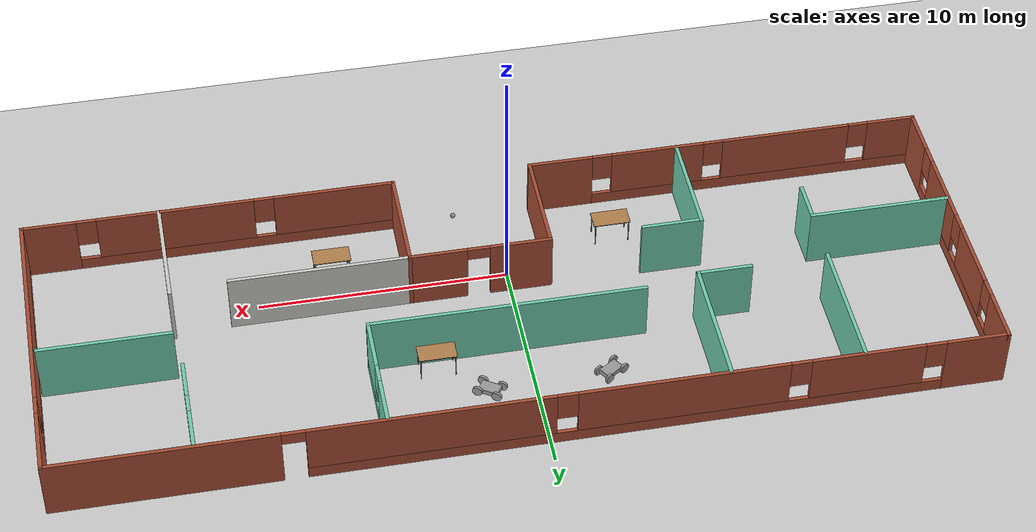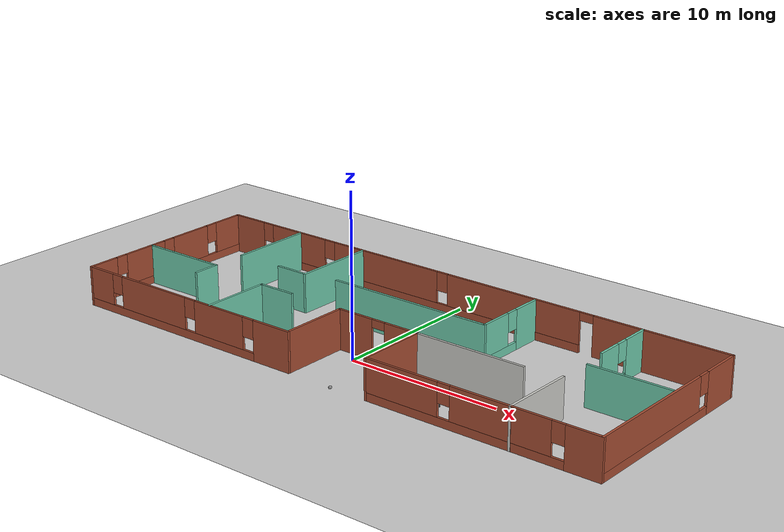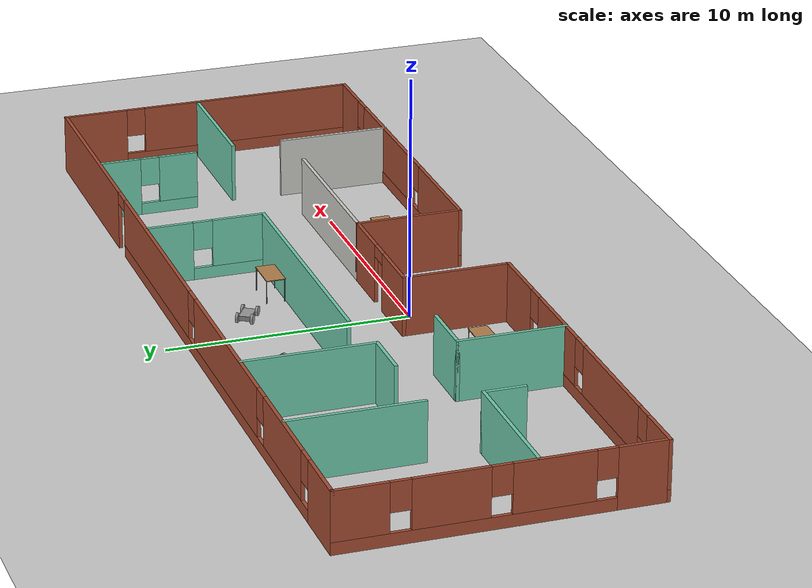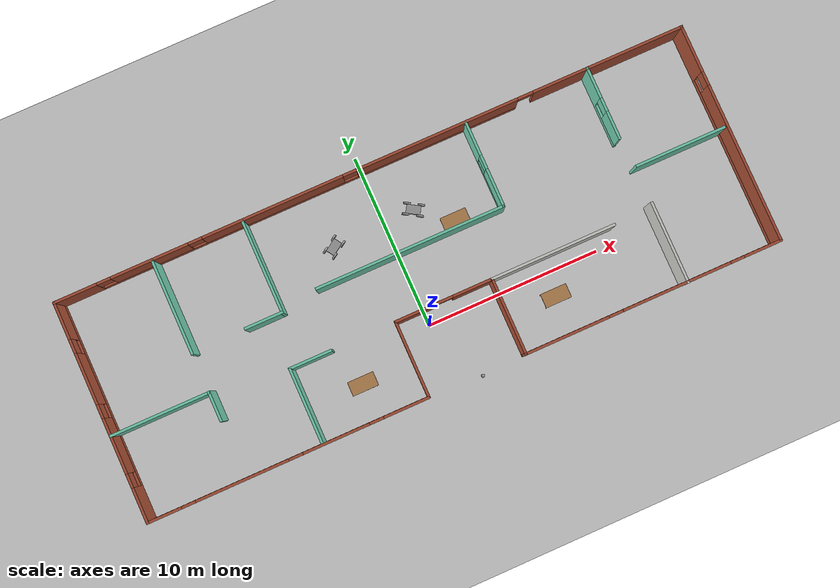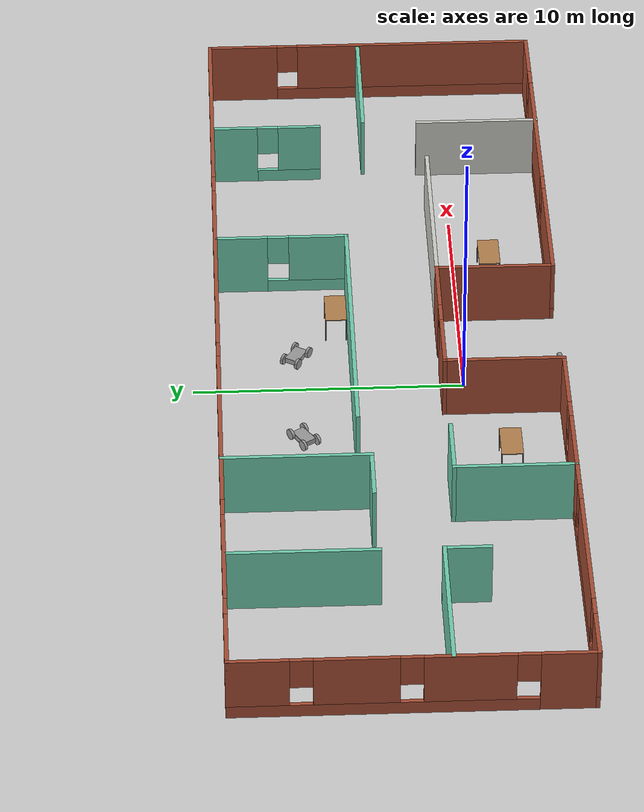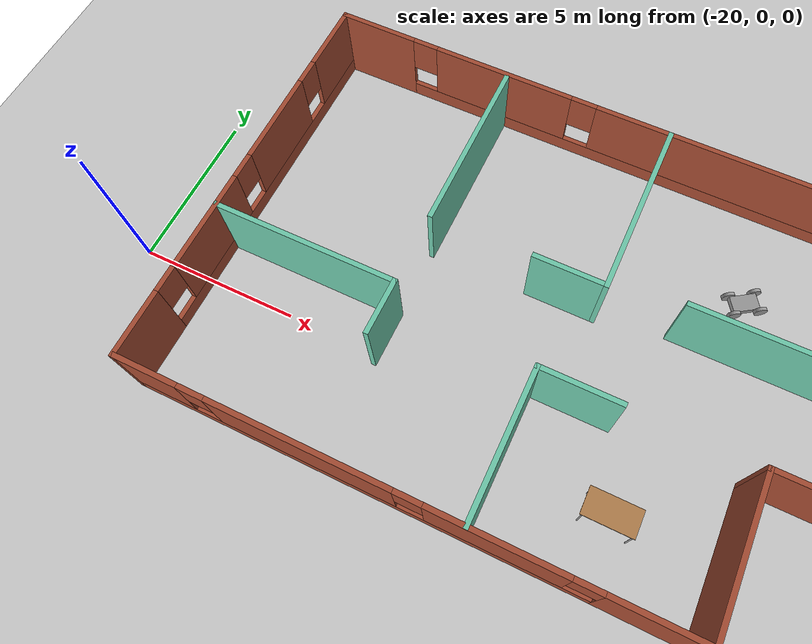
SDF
<sdf version="1.6">
 <world name="default">
  <plugin name="project" filename="libproject.so"/>
  <light name="sun" type="directional">
   <pose>0 0 10 0 -0 0</pose>
   <diffuse>0.8 0.8 0.8 1</diffuse>
   <specular>0.2 0.2 0.2 1</specular>
   <attenuation>
    <range>1000</range>
    <constant>0.9</constant>
    <linear>0.01</linear>
    <quadratic>0.001</quadratic>
   </attenuation>
   <direction>-0.5 0.1 -0.9</direction>
  </light>
  <model name="ground_plane">
   <static>1</static>
   <link name="link">
    <collision name="collision">
     <geometry><plane><normal>0 0 1</normal><size>100 100</size></plane></geometry>
     <surface><friction><ode><mu>100</mu><mu2>50</mu2></ode></friction></surface>
    </collision>
    <visual name="visual">
     <cast_shadows>0</cast_shadows>
     <geometry><plane><normal>0 0 1</normal><size>100 100</size></plane></geometry>
     <material>
      <script><uri>file://media/materials/scripts/gazebo.material</uri><name>Gazebo/Grey</name></script>
     </material>
    </visual>
   </link>
  </model>
  <gravity>0 0 -9.8</gravity>
  <magnetic_field>6e-06 2.3e-05 -4.2e-05</magnetic_field>
  <atmosphere type="adiabatic"/>
  <physics name="default_physics" default="0" type="ode">
   <max_step_size>0.001</max_step_size>
   <real_time_factor>1</real_time_factor>
   <real_time_update_rate>1000</real_time_update_rate>
  </physics>
  <scene><ambient>0.4 0.4 0.4 1</ambient><background>0.7 0.7 0.7 1</background><shadows>1</shadows></scene>
  <spherical_coordinates>
   <surface_model>EARTH_WGS84</surface_model>
   <latitude_deg>0</latitude_deg>
   <longitude_deg>0</longitude_deg>
   <elevation>0</elevation>
   <heading_deg>0</heading_deg>
  </spherical_coordinates>
  <model name="robot">
   <link name="link_0">
    <pose>0 -0 -0.015999 0 -0 0</pose>
    <inertial>
     <mass>1</mass>
     <inertia>
      <ixx>0.166667</ixx>
      <ixy>0</ixy>
      <ixz>0</ixz>
      <iyy>0.166667</iyy>
      <iyz>0</iyz>
      <izz>0.166667</izz>
     </inertia>
    </inertial>
    <visual name="visual">
     <geometry><box><size>0.8 0.5 0.2</size></box></geometry>
     <material>
      <lighting>1</lighting>
      <script><uri>file://media/materials/scripts/gazebo.material</uri><name>Gazebo/Grey</name></script>
      <shader type="pixel"><normal_map>__default__</normal_map></shader>
      <ambient>0.3 0.3 0.3 1</ambient>
      <diffuse>0.7 0.7 0.7 1</diffuse>
      <specular>0.01 0.01 0.01 1</specular>
      <emissive>0 0 0 1</emissive>
     </material>
    </visual>
    <collision name="collision">
     <geometry><box><size>0.8 0.5 0.2</size></box></geometry>
     <surface>
      <friction>
       <ode><mu>1</mu><mu2>1</mu2><fdir1>0 0 0</fdir1><slip1>0</slip1><slip2>0</slip2></ode>
       <torsional>
        <coefficient>1</coefficient>
        <patch_radius>0</patch_radius>
        <surface_radius>0</surface_radius>
        <use_patch_radius>1</use_patch_radius>
        <ode><slip>0</slip></ode>
       </torsional>
      </friction>
      <bounce><restitution_coefficient>0</restitution_coefficient><threshold>1e+06</threshold></bounce>
      <contact>
       <collide_without_contact>0</collide_without_contact>
       <collide_without_contact_bitmask>1</collide_without_contact_bitmask>
       <collide_bitmask>1</collide_bitmask>
       <ode>
        <soft_cfm>0</soft_cfm>
        <soft_erp>0.2</soft_erp>
        <kp>1e+13</kp>
        <kd>1</kd>
        <max_vel>0.01</max_vel>
        <min_depth>0</min_depth>
       </ode>
       <bullet>
        <split_impulse>1</split_impulse>
        <split_impulse_penetration_threshold>-0.01</split_impulse_penetration_threshold>
        <soft_cfm>0</soft_cfm>
        <soft_erp>0.2</soft_erp>
        <kp>1e+13</kp>
        <kd>1</kd>
       </bullet>
      </contact>
     </surface>
    </collision>
   </link>
   <link name="link_1">
    <pose>-0.4 -0.300019 0.003997 1.5707 -0 0</pose>
    <inertial>
     <mass>1</mass>
     <inertia><ixx>0.145833</ixx><ixy>0</ixy><ixz>0</ixz><iyy>0.145833</iyy><iyz>0</iyz><izz>0.125</izz></inertia>
    </inertial>
    <visual name="visual">
     <geometry><cylinder><radius>0.2</radius><length>0.1</length></cylinder></geometry>
     <material>
      <lighting>1</lighting>
      <script><uri>file://media/materials/scripts/gazebo.material</uri><name>Gazebo/Grey</name></script>
      <shader type="pixel"><normal_map>__default__</normal_map></shader>
      <ambient>0.3 0.3 0.3 1</ambient>
      <diffuse>0.7 0.7 0.7 1</diffuse>
      <specular>0.01 0.01 0.01 1</specular>
      <emissive>0 0 0 1</emissive>
     </material>
    </visual>
    <collision name="collision">
     <geometry><cylinder><radius>0.2</radius><length>0.1</length></cylinder></geometry>
     <surface>
      <friction>
       <ode><mu>1</mu><mu2>1</mu2><fdir1>0 0 0</fdir1><slip1>0</slip1><slip2>0</slip2></ode>
       <torsional>
        <coefficient>1</coefficient>
        <patch_radius>0</patch_radius>
        <surface_radius>0</surface_radius>
        <use_patch_radius>1</use_patch_radius>
        <ode><slip>0</slip></ode>
       </torsional>
      </friction>
      <bounce><restitution_coefficient>0</restitution_coefficient><threshold>1e+06</threshold></bounce>
      <contact>
       <collide_without_contact>0</collide_without_contact>
       <collide_without_contact_bitmask>1</collide_without_contact_bitmask>
       <collide_bitmask>1</collide_bitmask>
       <ode>
        <soft_cfm>0</soft_cfm>
        <soft_erp>0.2</soft_erp>
        <kp>1e+13</kp>
        <kd>1</kd>
        <max_vel>0.01</max_vel>
        <min_depth>0</min_depth>
       </ode>
       <bullet>
        <split_impulse>1</split_impulse>
        <split_impulse_penetration_threshold>-0.01</split_impulse_penetration_threshold>
        <soft_cfm>0</soft_cfm>
        <soft_erp>0.2</soft_erp>
        <kp>1e+13</kp>
        <kd>1</kd>
       </bullet>
      </contact>
     </surface>
    </collision>
   </link>
   <link name="link_1_clone">
    <pose>0.4 -0.300019 0.004001 1.5707 -0 0</pose>
    <inertial>
     <mass>1</mass>
     <inertia><ixx>0.145833</ixx><ixy>0</ixy><ixz>0</ixz><iyy>0.145833</iyy><iyz>0</iyz><izz>0.125</izz></inertia>
    </inertial>
    <visual name="visual">
     <geometry><cylinder><radius>0.2</radius><length>0.1</length></cylinder></geometry>
     <material>
      <lighting>1</lighting>
      <script><uri>file://media/materials/scripts/gazebo.material</uri><name>Gazebo/Grey</name></script>
      <shader type="pixel"><normal_map>__default__</normal_map></shader>
      <ambient>0.3 0.3 0.3 1</ambient>
      <diffuse>0.7 0.7 0.7 1</diffuse>
      <specular>0.01 0.01 0.01 1</specular>
      <emissive>0 0 0 1</emissive>
     </material>
    </visual>
    <collision name="collision">
     <geometry><cylinder><radius>0.2</radius><length>0.1</length></cylinder></geometry>
     <surface>
      <friction>
       <ode><mu>1</mu><mu2>1</mu2><fdir1>0 0 0</fdir1><slip1>0</slip1><slip2>0</slip2></ode>
       <torsional>
        <coefficient>1</coefficient>
        <patch_radius>0</patch_radius>
        <surface_radius>0</surface_radius>
        <use_patch_radius>1</use_patch_radius>
        <ode><slip>0</slip></ode>
       </torsional>
      </friction>
      <bounce><restitution_coefficient>0</restitution_coefficient><threshold>1e+06</threshold></bounce>
      <contact>
       <collide_without_contact>0</collide_without_contact>
       <collide_without_contact_bitmask>1</collide_without_contact_bitmask>
       <collide_bitmask>1</collide_bitmask>
       <ode>
        <soft_cfm>0</soft_cfm>
        <soft_erp>0.2</soft_erp>
        <kp>1e+13</kp>
        <kd>1</kd>
        <max_vel>0.01</max_vel>
        <min_depth>0</min_depth>
       </ode>
       <bullet>
        <split_impulse>1</split_impulse>
        <split_impulse_penetration_threshold>-0.01</split_impulse_penetration_threshold>
        <soft_cfm>0</soft_cfm>
        <soft_erp>0.2</soft_erp>
        <kp>1e+13</kp>
        <kd>1</kd>
       </bullet>
      </contact>
     </surface>
    </collision>
   </link>
   <link name="link_1_clone_1">
    <pose>0.4 0.300019 0.004001 1.5707 -0 0</pose>
    <inertial>
     <mass>1</mass>
     <inertia><ixx>0.145833</ixx><ixy>0</ixy><ixz>0</ixz><iyy>0.145833</iyy><iyz>0</iyz><izz>0.125</izz></inertia>
    </inertial>
    <visual name="visual">
     <geometry><cylinder><radius>0.2</radius><length>0.1</length></cylinder></geometry>
     <material>
      <lighting>1</lighting>
      <script><uri>file://media/materials/scripts/gazebo.material</uri><name>Gazebo/Grey</name></script>
      <shader type="pixel"><normal_map>__default__</normal_map></shader>
      <ambient>0.3 0.3 0.3 1</ambient>
      <diffuse>0.7 0.7 0.7 1</diffuse>
      <specular>0.01 0.01 0.01 1</specular>
      <emissive>0 0 0 1</emissive>
     </material>
    </visual>
    <collision name="collision">
     <geometry><cylinder><radius>0.2</radius><length>0.1</length></cylinder></geometry>
     <surface>
      <friction>
       <ode><mu>1</mu><mu2>1</mu2><fdir1>0 0 0</fdir1><slip1>0</slip1><slip2>0</slip2></ode>
       <torsional>
        <coefficient>1</coefficient>
        <patch_radius>0</patch_radius>
        <surface_radius>0</surface_radius>
        <use_patch_radius>1</use_patch_radius>
        <ode><slip>0</slip></ode>
       </torsional>
      </friction>
      <bounce><restitution_coefficient>0</restitution_coefficient><threshold>1e+06</threshold></bounce>
      <contact>
       <collide_without_contact>0</collide_without_contact>
       <collide_without_contact_bitmask>1</collide_without_contact_bitmask>
       <collide_bitmask>1</collide_bitmask>
       <ode>
        <soft_cfm>0</soft_cfm>
        <soft_erp>0.2</soft_erp>
        <kp>1e+13</kp>
        <kd>1</kd>
        <max_vel>0.01</max_vel>
        <min_depth>0</min_depth>
       </ode>
       <bullet>
        <split_impulse>1</split_impulse>
        <split_impulse_penetration_threshold>-0.01</split_impulse_penetration_threshold>
        <soft_cfm>0</soft_cfm>
        <soft_erp>0.2</soft_erp>
        <kp>1e+13</kp>
        <kd>1</kd>
       </bullet>
      </contact>
     </surface>
    </collision>
   </link>
   <link name="link_1_clone_1_clone">
    <pose>-0.4 0.300019 0.004001 1.5707 -0 0</pose>
    <inertial>
     <mass>1</mass>
     <inertia><ixx>0.145833</ixx><ixy>0</ixy><ixz>0</ixz><iyy>0.145833</iyy><iyz>0</iyz><izz>0.125</izz></inertia>
    </inertial>
    <visual name="visual">
     <geometry><cylinder><radius>0.2</radius><length>0.1</length></cylinder></geometry>
     <material>
      <lighting>1</lighting>
      <script><uri>file://media/materials/scripts/gazebo.material</uri><name>Gazebo/Grey</name></script>
      <shader type="pixel"><normal_map>__default__</normal_map></shader>
      <ambient>0.3 0.3 0.3 1</ambient>
      <diffuse>0.7 0.7 0.7 1</diffuse>
      <specular>0.01 0.01 0.01 1</specular>
      <emissive>0 0 0 1</emissive>
     </material>
    </visual>
    <collision name="collision">
     <geometry><cylinder><radius>0.2</radius><length>0.1</length></cylinder></geometry>
     <surface>
      <friction>
       <ode><mu>1</mu><mu2>1</mu2><fdir1>0 0 0</fdir1><slip1>0</slip1><slip2>0</slip2></ode>
       <torsional>
        <coefficient>1</coefficient>
        <patch_radius>0</patch_radius>
        <surface_radius>0</surface_radius>
        <use_patch_radius>1</use_patch_radius>
        <ode><slip>0</slip></ode>
       </torsional>
      </friction>
      <bounce><restitution_coefficient>0</restitution_coefficient><threshold>1e+06</threshold></bounce>
      <contact>
       <collide_without_contact>0</collide_without_contact>
       <collide_without_contact_bitmask>1</collide_without_contact_bitmask>
       <collide_bitmask>1</collide_bitmask>
       <ode>
        <soft_cfm>0</soft_cfm>
        <soft_erp>0.2</soft_erp>
        <kp>1e+13</kp>
        <kd>1</kd>
        <max_vel>0.01</max_vel>
        <min_depth>0</min_depth>
       </ode>
       <bullet>
        <split_impulse>1</split_impulse>
        <split_impulse_penetration_threshold>-0.01</split_impulse_penetration_threshold>
        <soft_cfm>0</soft_cfm>
        <soft_erp>0.2</soft_erp>
        <kp>1e+13</kp>
        <kd>1</kd>
       </bullet>
      </contact>
     </surface>
    </collision>
   </link>
   <joint name="link_0_JOINT_0" type="revolute">
    <parent>link_0</parent>
    <child>link_1</child>
    <axis>
     <xyz>0 0 1</xyz>
     <use_parent_model_frame>0</use_parent_model_frame>
     <limit>
      <lower>-1.79769e+308</lower>
      <upper>1.79769e+308</upper>
      <effort>-1</effort>
      <velocity>-1</velocity>
     </limit>
     <dynamics>
      <spring_reference>0</spring_reference>
      <spring_stiffness>0</spring_stiffness>
      <damping>0</damping>
     </dynamics>
    </axis>
    <physics>
     <ode><limit><cfm>0</cfm><erp>0.2</erp></limit><suspension><cfm>0</cfm><erp>0.2</erp></suspension></ode>
    </physics>
   </joint>
   <joint name="link_0_JOINT_3" type="revolute">
    <parent>link_0</parent>
    <child>link_1_clone_1_clone</child>
    <axis>
     <xyz>0 0 1</xyz>
     <use_parent_model_frame>0</use_parent_model_frame>
     <limit>
      <lower>-1.79769e+308</lower>
      <upper>1.79769e+308</upper>
      <effort>-1</effort>
      <velocity>-1</velocity>
     </limit>
     <dynamics>
      <spring_reference>0</spring_reference>
      <spring_stiffness>0</spring_stiffness>
      <damping>0</damping>
     </dynamics>
    </axis>
    <physics>
     <ode><limit><cfm>0</cfm><erp>0.2</erp></limit><suspension><cfm>0</cfm><erp>0.2</erp></suspension></ode>
    </physics>
   </joint>
   <joint name="link_0_JOINT_5" type="revolute">
    <parent>link_0</parent>
    <child>link_1_clone_1</child>
    <axis>
     <xyz>0 0 1</xyz>
     <use_parent_model_frame>0</use_parent_model_frame>
     <limit>
      <lower>-1.79769e+308</lower>
      <upper>1.79769e+308</upper>
      <effort>-1</effort>
      <velocity>-1</velocity>
     </limit>
     <dynamics>
      <spring_reference>0</spring_reference>
      <spring_stiffness>0</spring_stiffness>
      <damping>0</damping>
     </dynamics>
    </axis>
    <physics>
     <ode><limit><cfm>0</cfm><erp>0.2</erp></limit><suspension><cfm>0</cfm><erp>0.2</erp></suspension></ode>
    </physics>
   </joint>
   <joint name="link_0_JOINT_6" type="revolute">
    <parent>link_0</parent>
    <child>link_1_clone</child>
    <axis>
     <xyz>0 0 1</xyz>
     <use_parent_model_frame>0</use_parent_model_frame>
     <limit>
      <lower>-1.79769e+308</lower>
      <upper>1.79769e+308</upper>
      <effort>-1</effort>
      <velocity>-1</velocity>
     </limit>
     <dynamics>
      <spring_reference>0</spring_reference>
      <spring_stiffness>0</spring_stiffness>
      <damping>0</damping>
     </dynamics>
    </axis>
    <physics>
     <ode><limit><cfm>0</cfm><erp>0.2</erp></limit><suspension><cfm>0</cfm><erp>0.2</erp></suspension></ode>
    </physics>
   </joint>
   <static>0</static>
   <pose>-2.99375 6.00403 0.196005 -4e-06 5e-06 -2.55933</pose>
  </model>
  <model name="office">
   <pose>0.5777 2.7439 0 0 -0 0</pose>
   <link name="Wall_27">
    <pose>18.275 0.006607 0 0 0 -1.5708</pose>
    <visual name="Wall_27_Visual_0">
     <pose>-4.99868 0 1.25 0 -0 0</pose>
     <geometry><box><size>2.75264 0.15 2.5</size></box></geometry>
     <material>
      <script><uri>file://media/materials/scripts/gazebo.material</uri><name>Gazebo/Bricks</name></script>
      <ambient>1 1 1 1</ambient>
     </material>
     <meta><layer>0</layer></meta>
    </visual>
    <collision name="Wall_27_Collision_0">
     <geometry><box><size>2.75264 0.15 2.5</size></box></geometry>
     <pose>-4.99868 0 1.25 0 -0 0</pose>
    </collision>
    <visual name="Wall_27_Visual_1">
     <pose>1.37632 0 0.25 0 -0 0</pose>
     <geometry><box><size>9.99736 0.15 0.5</size></box></geometry>
     <material>
      <script><uri>file://media/materials/scripts/gazebo.material</uri><name>Gazebo/Bricks</name></script>
      <ambient>1 1 1 1</ambient>
     </material>
     <meta><layer>0</layer></meta>
    </visual>
    <collision name="Wall_27_Collision_1">
     <geometry><box><size>9.99736 0.15 0.5</size></box></geometry>
     <pose>1.37632 0 0.25 0 -0 0</pose>
    </collision>
    <visual name="Wall_27_Visual_2">
     <pose>1.77632 0 1.5 0 -0 0</pose>
     <geometry><box><size>9.19736 0.15 2</size></box></geometry>
     <material>
      <script><uri>file://media/materials/scripts/gazebo.material</uri><name>Gazebo/Bricks</name></script>
      <ambient>1 1 1 1</ambient>
     </material>
     <meta><layer>0</layer></meta>
    </visual>
    <collision name="Wall_27_Collision_2">
     <geometry><box><size>9.19736 0.15 2</size></box></geometry>
     <pose>1.77632 0 1.5 0 -0 0</pose>
    </collision>
    <visual name="Wall_27_Visual_3">
     <pose>-3.22236 0 1.9 0 -0 0</pose>
     <geometry><box><size>0.8 0.15 1.2</size></box></geometry>
     <material>
      <script><uri>file://media/materials/scripts/gazebo.material</uri><name>Gazebo/Bricks</name></script>
      <ambient>1 1 1 1</ambient>
     </material>
     <meta><layer>0</layer></meta>
    </visual>
    <collision name="Wall_27_Collision_3">
     <geometry><box><size>0.8 0.15 1.2</size></box></geometry>
     <pose>-3.22236 0 1.9 0 -0 0</pose>
    </collision>
   </link>
   <link name="Wall_28">
    <pose>10.85 -6.29339 0 0 -0 3.14159</pose>
    <visual name="Wall_28_Visual_0">
     <pose>-6.39219 0 1.25 0 -0 0</pose>
     <geometry><box><size>2.21562 0.15 2.5</size></box></geometry>
     <material>
      <script><uri>file://media/materials/scripts/gazebo.material</uri><name>Gazebo/Bricks</name></script>
      <ambient>1 1 1 1</ambient>
     </material>
     <meta><layer>0</layer></meta>
    </visual>
    <collision name="Wall_28_Collision_0">
     <geometry><box><size>2.21562 0.15 2.5</size></box></geometry>
     <pose>-6.39219 0 1.25 0 -0 0</pose>
    </collision>
    <visual name="Wall_28_Visual_1">
     <pose>1.10781 0 0.25 0 -0 0</pose>
     <geometry><box><size>12.7844 0.15 0.5</size></box></geometry>
     <material>
      <script><uri>file://media/materials/scripts/gazebo.material</uri><name>Gazebo/Bricks</name></script>
      <ambient>1 1 1 1</ambient>
     </material>
     <meta><layer>0</layer></meta>
    </visual>
    <collision name="Wall_28_Collision_1">
     <geometry><box><size>12.7844 0.15 0.5</size></box></geometry>
     <pose>1.10781 0 0.25 0 -0 0</pose>
    </collision>
    <visual name="Wall_28_Visual_2">
     <pose>-1.34653 0 1.5 0 -0 0</pose>
     <geometry><box><size>6.27571 0.15 2</size></box></geometry>
     <material>
      <script><uri>file://media/materials/scripts/gazebo.material</uri><name>Gazebo/Bricks</name></script>
      <ambient>1 1 1 1</ambient>
     </material>
     <meta><layer>0</layer></meta>
    </visual>
    <collision name="Wall_28_Collision_2">
     <geometry><box><size>6.27571 0.15 2</size></box></geometry>
     <pose>-1.34653 0 1.5 0 -0 0</pose>
    </collision>
    <visual name="Wall_28_Visual_3">
     <pose>5.04566 0 1.5 0 -0 0</pose>
     <geometry><box><size>4.90868 0.15 2</size></box></geometry>
     <material>
      <script><uri>file://media/materials/scripts/gazebo.material</uri><name>Gazebo/Bricks</name></script>
      <ambient>1 1 1 1</ambient>
     </material>
     <meta><layer>0</layer></meta>
    </visual>
    <collision name="Wall_28_Collision_3">
     <geometry><box><size>4.90868 0.15 2</size></box></geometry>
     <pose>5.04566 0 1.5 0 -0 0</pose>
    </collision>
    <visual name="Wall_28_Visual_4">
     <pose>-4.88438 0 1.9 0 -0 0</pose>
     <geometry><box><size>0.8 0.15 1.2</size></box></geometry>
     <material>
      <script><uri>file://media/materials/scripts/gazebo.material</uri><name>Gazebo/Bricks</name></script>
      <ambient>1 1 1 1</ambient>
     </material>
     <meta><layer>0</layer></meta>
    </visual>
    <collision name="Wall_28_Collision_4">
     <geometry><box><size>0.8 0.15 1.2</size></box></geometry>
     <pose>-4.88438 0 1.9 0 -0 0</pose>
    </collision>
    <visual name="Wall_28_Visual_5">
     <pose>2.19132 0 1.9 0 -0 0</pose>
     <geometry><box><size>0.8 0.15 1.2</size></box></geometry>
     <material>
      <script><uri>file://media/materials/scripts/gazebo.material</uri><name>Gazebo/Bricks</name></script>
      <ambient>1 1 1 1</ambient>
     </material>
     <meta><layer>0</layer></meta>
    </visual>
    <collision name="Wall_28_Collision_5">
     <geometry><box><size>0.8 0.15 1.2</size></box></geometry>
     <pose>2.19132 0 1.9 0 -0 0</pose>
    </collision>
   </link>
   <link name="Wall_29">
    <collision name="Wall_29_Collision">
     <geometry><box><size>4.5 0.15 2.5</size></box></geometry>
     <pose>0 0 1.25 0 -0 0</pose>
    </collision>
    <visual name="Wall_29_Visual">
     <pose>0 0 1.25 0 -0 0</pose>
     <geometry><box><size>4.5 0.15 2.5</size></box></geometry>
     <material>
      <script><uri>file://media/materials/scripts/gazebo.material</uri><name>Gazebo/Bricks</name></script>
      <ambient>1 1 1 1</ambient>
     </material>
     <meta><layer>0</layer></meta>
    </visual>
    <pose>3.425 -4.11839 0 0 -0 1.5708</pose>
   </link>
   <link name="Wall_30">
    <pose>0.625 -1.94339 0 0 -0 3.14159</pose>
    <visual name="Wall_30_Visual_0">
     <pose>-1.6967 0 1.25 0 -0 0</pose>
     <geometry><box><size>2.3566 0.15 2.5</size></box></geometry>
     <material>
      <script><uri>file://media/materials/scripts/gazebo.material</uri><name>Gazebo/Bricks</name></script>
      <ambient>1 1 1 1</ambient>
     </material>
     <meta><layer>0</layer></meta>
    </visual>
    <collision name="Wall_30_Collision_0">
     <geometry><box><size>2.3566 0.15 2.5</size></box></geometry>
     <pose>-1.6967 0 1.25 0 -0 0</pose>
    </collision>
    <visual name="Wall_30_Visual_1">
     <pose>1.6283 0 1.25 0 -0 0</pose>
     <geometry><box><size>2.4934 0.15 2.5</size></box></geometry>
     <material>
      <script><uri>file://media/materials/scripts/gazebo.material</uri><name>Gazebo/Bricks</name></script>
      <ambient>1 1 1 1</ambient>
     </material>
     <meta><layer>0</layer></meta>
    </visual>
    <collision name="Wall_30_Collision_1">
     <geometry><box><size>2.4934 0.15 2.5</size></box></geometry>
     <pose>1.6283 0 1.25 0 -0 0</pose>
    </collision>
    <visual name="Wall_30_Visual_2">
     <pose>-0.068397 0 2.25 0 -0 0</pose>
     <geometry><box><size>0.9 0.15 0.5</size></box></geometry>
     <material>
      <script><uri>file://media/materials/scripts/gazebo.material</uri><name>Gazebo/Bricks</name></script>
      <ambient>1 1 1 1</ambient>
     </material>
     <meta><layer>0</layer></meta>
    </visual>
    <collision name="Wall_30_Collision_2">
     <geometry><box><size>0.9 0.15 0.5</size></box></geometry>
     <pose>-0.068397 0 2.25 0 -0 0</pose>
    </collision>
   </link>
   <link name="Wall_31">
    <collision name="Wall_31_Collision">
     <geometry><box><size>4.5 0.15 2.5</size></box></geometry>
     <pose>0 0 1.25 0 -0 0</pose>
    </collision>
    <visual name="Wall_31_Visual">
     <pose>0 0 1.25 0 -0 0</pose>
     <geometry><box><size>4.5 0.15 2.5</size></box></geometry>
     <material>
      <script><uri>file://media/materials/scripts/gazebo.material</uri><name>Gazebo/Bricks</name></script>
      <ambient>1 1 1 1</ambient>
     </material>
     <meta><layer>0</layer></meta>
    </visual>
    <pose>-2.175 -4.11839 0 0 0 -1.5708</pose>
   </link>
   <link name="Wall_32">
    <pose>-10.225 -6.29339 0 0 -0 3.14159</pose>
    <visual name="Wall_32_Visual_0">
     <pose>-6.78571 0 1.25 0 -0 0</pose>
     <geometry><box><size>2.67859 0.15 2.5</size></box></geometry>
     <material>
      <script><uri>file://media/materials/scripts/gazebo.material</uri><name>Gazebo/Bricks</name></script>
      <ambient>1 1 1 1</ambient>
     </material>
     <meta><layer>0</layer></meta>
    </visual>
    <collision name="Wall_32_Collision_0">
     <geometry><box><size>2.67859 0.15 2.5</size></box></geometry>
     <pose>-6.78571 0 1.25 0 -0 0</pose>
    </collision>
    <visual name="Wall_32_Visual_1">
     <pose>1.33929 0 0.25 0 -0 0</pose>
     <geometry><box><size>13.5714 0.15 0.5</size></box></geometry>
     <material>
      <script><uri>file://media/materials/scripts/gazebo.material</uri><name>Gazebo/Bricks</name></script>
      <ambient>1 1 1 1</ambient>
     </material>
     <meta><layer>0</layer></meta>
    </visual>
    <collision name="Wall_32_Collision_1">
     <geometry><box><size>13.5714 0.15 0.5</size></box></geometry>
     <pose>1.33929 0 0.25 0 -0 0</pose>
    </collision>
    <visual name="Wall_32_Visual_2">
     <pose>-2.72912 0 1.5 0 -0 0</pose>
     <geometry><box><size>3.83459 0.15 2</size></box></geometry>
     <material>
      <script><uri>file://media/materials/scripts/gazebo.material</uri><name>Gazebo/Bricks</name></script>
      <ambient>1 1 1 1</ambient>
     </material>
     <meta><layer>0</layer></meta>
    </visual>
    <collision name="Wall_32_Collision_2">
     <geometry><box><size>3.83459 0.15 2</size></box></geometry>
     <pose>-2.72912 0 1.5 0 -0 0</pose>
    </collision>
    <visual name="Wall_32_Visual_3">
     <pose>2.64842 0 1.5 0 -0 0</pose>
     <geometry><box><size>5.32049 0.15 2</size></box></geometry>
     <material>
      <script><uri>file://media/materials/scripts/gazebo.material</uri><name>Gazebo/Bricks</name></script>
      <ambient>1 1 1 1</ambient>
     </material>
     <meta><layer>0</layer></meta>
    </visual>
    <collision name="Wall_32_Collision_3">
     <geometry><box><size>5.32049 0.15 2</size></box></geometry>
     <pose>2.64842 0 1.5 0 -0 0</pose>
    </collision>
    <visual name="Wall_32_Visual_4">
     <pose>7.11683 0 1.5 0 -0 0</pose>
     <geometry><box><size>2.01634 0.15 2</size></box></geometry>
     <material>
      <script><uri>file://media/materials/scripts/gazebo.material</uri><name>Gazebo/Bricks</name></script>
      <ambient>1 1 1 1</ambient>
     </material>
     <meta><layer>0</layer></meta>
    </visual>
    <collision name="Wall_32_Collision_4">
     <geometry><box><size>2.01634 0.15 2</size></box></geometry>
     <pose>7.11683 0 1.5 0 -0 0</pose>
    </collision>
    <visual name="Wall_32_Visual_5">
     <pose>-5.04641 0 1.9 0 -0 0</pose>
     <geometry><box><size>0.8 0.15 1.2</size></box></geometry>
     <material>
      <script><uri>file://media/materials/scripts/gazebo.material</uri><name>Gazebo/Bricks</name></script>
      <ambient>1 1 1 1</ambient>
     </material>
     <meta><layer>0</layer></meta>
    </visual>
    <collision name="Wall_32_Collision_5">
     <geometry><box><size>0.8 0.15 1.2</size></box></geometry>
     <pose>-5.04641 0 1.9 0 -0 0</pose>
    </collision>
    <visual name="Wall_32_Visual_6">
     <pose>-0.411825 0 1.9 0 -0 0</pose>
     <geometry><box><size>0.8 0.15 1.2</size></box></geometry>
     <material>
      <script><uri>file://media/materials/scripts/gazebo.material</uri><name>Gazebo/Bricks</name></script>
      <ambient>1 1 1 1</ambient>
     </material>
     <meta><layer>0</layer></meta>
    </visual>
    <collision name="Wall_32_Collision_6">
     <geometry><box><size>0.8 0.15 1.2</size></box></geometry>
     <pose>-0.411825 0 1.9 0 -0 0</pose>
    </collision>
    <visual name="Wall_32_Visual_7">
     <pose>5.70866 0 1.9 0 -0 0</pose>
     <geometry><box><size>0.8 0.15 1.2</size></box></geometry>
     <material>
      <script><uri>file://media/materials/scripts/gazebo.material</uri><name>Gazebo/Bricks</name></script>
      <ambient>1 1 1 1</ambient>
     </material>
     <meta><layer>0</layer></meta>
    </visual>
    <collision name="Wall_32_Collision_7">
     <geometry><box><size>0.8 0.15 1.2</size></box></geometry>
     <pose>5.70866 0 1.9 0 -0 0</pose>
    </collision>
   </link>
   <link name="Wall_33">
    <pose>-18.275 0.006607 0 0 -0 1.5708</pose>
    <visual name="Wall_33_Visual_0">
     <pose>-5.34955 0 1.25 0 -0 0</pose>
     <geometry><box><size>2.0509 0.15 2.5</size></box></geometry>
     <material>
      <script><uri>file://media/materials/scripts/gazebo.material</uri><name>Gazebo/Bricks</name></script>
      <ambient>1 1 1 1</ambient>
     </material>
     <meta><layer>0</layer></meta>
    </visual>
    <collision name="Wall_33_Collision_0">
     <geometry><box><size>2.0509 0.15 2.5</size></box></geometry>
     <pose>-5.34955 0 1.25 0 -0 0</pose>
    </collision>
    <visual name="Wall_33_Visual_1">
     <pose>1.02545 0 0.25 0 -0 0</pose>
     <geometry><box><size>10.6991 0.15 0.5</size></box></geometry>
     <material>
      <script><uri>file://media/materials/scripts/gazebo.material</uri><name>Gazebo/Bricks</name></script>
      <ambient>1 1 1 1</ambient>
     </material>
     <meta><layer>0</layer></meta>
    </visual>
    <collision name="Wall_33_Collision_1">
     <geometry><box><size>10.6991 0.15 0.5</size></box></geometry>
     <pose>1.02545 0 0.25 0 -0 0</pose>
    </collision>
    <visual name="Wall_33_Visual_2">
     <pose>-1.9429 0 1.5 0 -0 0</pose>
     <geometry><box><size>3.1624 0.15 2</size></box></geometry>
     <material>
      <script><uri>file://media/materials/scripts/gazebo.material</uri><name>Gazebo/Bricks</name></script>
      <ambient>1 1 1 1</ambient>
     </material>
     <meta><layer>0</layer></meta>
    </visual>
    <collision name="Wall_33_Collision_2">
     <geometry><box><size>3.1624 0.15 2</size></box></geometry>
     <pose>-1.9429 0 1.5 0 -0 0</pose>
    </collision>
    <visual name="Wall_33_Visual_3">
     <pose>1.91336 0 1.5 0 -0 0</pose>
     <geometry><box><size>2.95012 0.15 2</size></box></geometry>
     <material>
      <script><uri>file://media/materials/scripts/gazebo.material</uri><name>Gazebo/Bricks</name></script>
      <ambient>1 1 1 1</ambient>
     </material>
     <meta><layer>0</layer></meta>
    </visual>
    <collision name="Wall_33_Collision_3">
     <geometry><box><size>2.95012 0.15 2</size></box></geometry>
     <pose>1.91336 0 1.5 0 -0 0</pose>
    </collision>
    <visual name="Wall_33_Visual_4">
     <pose>5.28171 0 1.5 0 -0 0</pose>
     <geometry><box><size>2.18658 0.15 2</size></box></geometry>
     <material>
      <script><uri>file://media/materials/scripts/gazebo.material</uri><name>Gazebo/Bricks</name></script>
      <ambient>1 1 1 1</ambient>
     </material>
     <meta><layer>0</layer></meta>
    </visual>
    <collision name="Wall_33_Collision_4">
     <geometry><box><size>2.18658 0.15 2</size></box></geometry>
     <pose>5.28171 0 1.5 0 -0 0</pose>
    </collision>
    <visual name="Wall_33_Visual_5">
     <pose>-3.9241 0 1.9 0 -0 0</pose>
     <geometry><box><size>0.8 0.15 1.2</size></box></geometry>
     <material>
      <script><uri>file://media/materials/scripts/gazebo.material</uri><name>Gazebo/Bricks</name></script>
      <ambient>1 1 1 1</ambient>
     </material>
     <meta><layer>0</layer></meta>
    </visual>
    <collision name="Wall_33_Collision_5">
     <geometry><box><size>0.8 0.15 1.2</size></box></geometry>
     <pose>-3.9241 0 1.9 0 -0 0</pose>
    </collision>
    <visual name="Wall_33_Visual_6">
     <pose>0.038294 0 1.9 0 -0 0</pose>
     <geometry><box><size>0.8 0.15 1.2</size></box></geometry>
     <material>
      <script><uri>file://media/materials/scripts/gazebo.material</uri><name>Gazebo/Bricks</name></script>
      <ambient>1 1 1 1</ambient>
     </material>
     <meta><layer>0</layer></meta>
    </visual>
    <collision name="Wall_33_Collision_6">
     <geometry><box><size>0.8 0.15 1.2</size></box></geometry>
     <pose>0.038294 0 1.9 0 -0 0</pose>
    </collision>
    <visual name="Wall_33_Visual_7">
     <pose>3.78842 0 1.9 0 -0 0</pose>
     <geometry><box><size>0.8 0.15 1.2</size></box></geometry>
     <material>
      <script><uri>file://media/materials/scripts/gazebo.material</uri><name>Gazebo/Bricks</name></script>
      <ambient>1 1 1 1</ambient>
     </material>
     <meta><layer>0</layer></meta>
    </visual>
    <collision name="Wall_33_Collision_7">
     <geometry><box><size>0.8 0.15 1.2</size></box></geometry>
     <pose>3.78842 0 1.9 0 -0 0</pose>
    </collision>
   </link>
   <link name="Wall_35">
    <pose>0 6.30661 0 0 -0 0</pose>
    <visual name="Wall_35_Visual_0">
     <pose>-17.0942 0 1.25 0 -0 0</pose>
     <geometry><box><size>2.51164 0.15 2.5</size></box></geometry>
     <material>
      <script><uri>file://media/materials/scripts/gazebo.material</uri><name>Gazebo/Bricks</name></script>
      <ambient>1 1 1 1</ambient>
     </material>
     <meta><layer>0</layer></meta>
    </visual>
    <collision name="Wall_35_Collision_0">
     <geometry><box><size>2.51164 0.15 2.5</size></box></geometry>
     <pose>-17.0942 0 1.25 0 -0 0</pose>
    </collision>
    <visual name="Wall_35_Visual_1">
     <pose>13.9356 0 1.25 0 -0 0</pose>
     <geometry><box><size>8.82887 0.15 2.5</size></box></geometry>
     <material>
      <script><uri>file://media/materials/scripts/gazebo.material</uri><name>Gazebo/Bricks</name></script>
      <ambient>1 1 1 1</ambient>
     </material>
     <meta><layer>0</layer></meta>
    </visual>
    <collision name="Wall_35_Collision_1">
     <geometry><box><size>8.82887 0.15 2.5</size></box></geometry>
     <pose>13.9356 0 1.25 0 -0 0</pose>
    </collision>
    <visual name="Wall_35_Visual_2">
     <pose>-3.60861 0 0.25 0 -0 0</pose>
     <geometry><box><size>24.4595 0.15 0.5</size></box></geometry>
     <material>
      <script><uri>file://media/materials/scripts/gazebo.material</uri><name>Gazebo/Bricks</name></script>
      <ambient>1 1 1 1</ambient>
     </material>
     <meta><layer>0</layer></meta>
    </visual>
    <collision name="Wall_35_Collision_2">
     <geometry><box><size>24.4595 0.15 0.5</size></box></geometry>
     <pose>-3.60861 0 0.25 0 -0 0</pose>
    </collision>
    <visual name="Wall_35_Visual_3">
     <pose>-12.8027 0 1.5 0 -0 0</pose>
     <geometry><box><size>4.4714 0.15 2</size></box></geometry>
     <material>
      <script><uri>file://media/materials/scripts/gazebo.material</uri><name>Gazebo/Bricks</name></script>
      <ambient>1 1 1 1</ambient>
     </material>
     <meta><layer>0</layer></meta>
    </visual>
    <collision name="Wall_35_Collision_3">
     <geometry><box><size>4.4714 0.15 2</size></box></geometry>
     <pose>-12.8027 0 1.5 0 -0 0</pose>
    </collision>
    <visual name="Wall_35_Visual_4">
     <pose>-5.68356 0 1.5 0 -0 0</pose>
     <geometry><box><size>8.16679 0.15 2</size></box></geometry>
     <material>
      <script><uri>file://media/materials/scripts/gazebo.material</uri><name>Gazebo/Bricks</name></script>
      <ambient>1 1 1 1</ambient>
     </material>
     <meta><layer>0</layer></meta>
    </visual>
    <collision name="Wall_35_Collision_4">
     <geometry><box><size>8.16679 0.15 2</size></box></geometry>
     <pose>-5.68356 0 1.5 0 -0 0</pose>
    </collision>
    <visual name="Wall_35_Visual_5">
     <pose>3.91048 0 1.5 0 -0 0</pose>
     <geometry><box><size>9.4213 0.15 2</size></box></geometry>
     <material>
      <script><uri>file://media/materials/scripts/gazebo.material</uri><name>Gazebo/Bricks</name></script>
      <ambient>1 1 1 1</ambient>
     </material>
     <meta><layer>0</layer></meta>
    </visual>
    <collision name="Wall_35_Collision_5">
     <geometry><box><size>9.4213 0.15 2</size></box></geometry>
     <pose>3.91048 0 1.5 0 -0 0</pose>
    </collision>
    <visual name="Wall_35_Visual_6">
     <pose>-15.4384 0 1.9 0 -0 0</pose>
     <geometry><box><size>0.8 0.15 1.2</size></box></geometry>
     <material>
      <script><uri>file://media/materials/scripts/gazebo.material</uri><name>Gazebo/Bricks</name></script>
      <ambient>1 1 1 1</ambient>
     </material>
     <meta><layer>0</layer></meta>
    </visual>
    <collision name="Wall_35_Collision_6">
     <geometry><box><size>0.8 0.15 1.2</size></box></geometry>
     <pose>-15.4384 0 1.9 0 -0 0</pose>
    </collision>
    <visual name="Wall_35_Visual_7">
     <pose>-10.167 0 1.9 0 -0 0</pose>
     <geometry><box><size>0.8 0.15 1.2</size></box></geometry>
     <material>
      <script><uri>file://media/materials/scripts/gazebo.material</uri><name>Gazebo/Bricks</name></script>
      <ambient>1 1 1 1</ambient>
     </material>
     <meta><layer>0</layer></meta>
    </visual>
    <collision name="Wall_35_Collision_7">
     <geometry><box><size>0.8 0.15 1.2</size></box></geometry>
     <pose>-10.167 0 1.9 0 -0 0</pose>
    </collision>
    <visual name="Wall_35_Visual_8">
     <pose>-1.20017 0 1.9 0 -0 0</pose>
     <geometry><box><size>0.8 0.15 1.2</size></box></geometry>
     <material>
      <script><uri>file://media/materials/scripts/gazebo.material</uri><name>Gazebo/Bricks</name></script>
      <ambient>1 1 1 1</ambient>
     </material>
     <meta><layer>0</layer></meta>
    </visual>
    <collision name="Wall_35_Collision_8">
     <geometry><box><size>0.8 0.15 1.2</size></box></geometry>
     <pose>-1.20017 0 1.9 0 -0 0</pose>
    </collision>
    <visual name="Wall_35_Visual_9">
     <pose>9.07113 0 2.25 0 -0 0</pose>
     <geometry><box><size>0.9 0.15 0.5</size></box></geometry>
     <material>
      <script><uri>file://media/materials/scripts/gazebo.material</uri><name>Gazebo/Bricks</name></script>
      <ambient>1 1 1 1</ambient>
     </material>
     <meta><layer>0</layer></meta>
    </visual>
    <collision name="Wall_35_Collision_9">
     <geometry><box><size>0.9 0.15 0.5</size></box></geometry>
     <pose>9.07113 0 2.25 0 -0 0</pose>
    </collision>
   </link>
   <link name="Wall_38">
    <collision name="Wall_38_Collision">
     <geometry><box><size>5.75 0.15 2.5</size></box></geometry>
     <pose>0 0 1.25 0 -0 0</pose>
    </collision>
    <visual name="Wall_38_Visual">
     <pose>0 0 1.25 0 -0 0</pose>
     <geometry><box><size>5.75 0.15 2.5</size></box></geometry>
     <material>
      <script><uri>file://media/materials/scripts/gazebo.material</uri><name>Gazebo/Grey</name></script>
      <ambient>0.435294 0.796078 0.67451 1</ambient>
     </material>
     <meta><layer>0</layer></meta>
    </visual>
    <pose>-15.4596 -1.35361 0 0 -0 0</pose>
   </link>
   <link name="Wall_39">
    <collision name="Wall_39_Collision">
     <geometry><box><size>1.75 0.15 2.5</size></box></geometry>
     <pose>0 0 1.25 0 -0 0</pose>
    </collision>
    <visual name="Wall_39_Visual">
     <pose>0 0 1.25 0 -0 0</pose>
     <geometry><box><size>1.75 0.15 2.5</size></box></geometry>
     <material>
      <script><uri>file://media/materials/scripts/gazebo.material</uri><name>Gazebo/Grey</name></script>
      <ambient>0.435294 0.796078 0.67451 1</ambient>
     </material>
     <meta><layer>0</layer></meta>
    </visual>
    <pose>-12.6596 -2.15361 0 0 0 -1.5708</pose>
   </link>
   <link name="Wall_41">
    <collision name="Wall_41_Collision">
     <geometry><box><size>5.5 0.15 2.5</size></box></geometry>
     <pose>0 0 1.25 0 -0 0</pose>
    </collision>
    <visual name="Wall_41_Visual">
     <pose>0 0 1.25 0 -0 0</pose>
     <geometry><box><size>5.5 0.15 2.5</size></box></geometry>
     <material>
      <script><uri>file://media/materials/scripts/gazebo.material</uri><name>Gazebo/Grey</name></script>
      <ambient>0.435294 0.796078 0.67451 1</ambient>
     </material>
     <meta><layer>0</layer></meta>
    </visual>
    <pose>-12.6605 3.57008 0 0 0 -1.5708</pose>
   </link>
   <link name="Wall_43">
    <collision name="Wall_43_Collision">
     <geometry><box><size>2.25 0.15 2.5</size></box></geometry>
     <pose>0 0 1.25 0 -0 0</pose>
    </collision>
    <visual name="Wall_43_Visual">
     <pose>0 0 1.25 0 -0 0</pose>
     <geometry><box><size>2.25 0.15 2.5</size></box></geometry>
     <material>
      <script><uri>file://media/materials/scripts/gazebo.material</uri><name>Gazebo/Grey</name></script>
      <ambient>0.435294 0.796078 0.67451 1</ambient>
     </material>
     <meta><layer>0</layer></meta>
    </visual>
    <pose>-8.50339 0.953682 0 0 -0 0</pose>
   </link>
   <link name="Wall_44">
    <collision name="Wall_44_Collision">
     <geometry><box><size>5.5 0.15 2.5</size></box></geometry>
     <pose>0 0 1.25 0 -0 0</pose>
    </collision>
    <visual name="Wall_44_Visual">
     <pose>0 0 1.25 0 -0 0</pose>
     <geometry><box><size>5.5 0.15 2.5</size></box></geometry>
     <material>
      <script><uri>file://media/materials/scripts/gazebo.material</uri><name>Gazebo/Grey</name></script>
      <ambient>0.435294 0.796078 0.67451 1</ambient>
     </material>
     <meta><layer>0</layer></meta>
    </visual>
    <pose>-7.45339 3.62868 0 0 -0 1.5708</pose>
   </link>
   <link name="Wall_46">
    <collision name="Wall_46_Collision">
     <geometry><box><size>4.75 0.15 2.5</size></box></geometry>
     <pose>0 0 1.25 0 -0 0</pose>
    </collision>
    <visual name="Wall_46_Visual">
     <pose>0 0 1.25 0 -0 0</pose>
     <geometry><box><size>4.75 0.15 2.5</size></box></geometry>
     <material>
      <script><uri>file://media/materials/scripts/gazebo.material</uri><name>Gazebo/CeilingTiled</name></script>
      <ambient>0.435294 0.796078 0.67451 1</ambient>
     </material>
     <meta><layer>0</layer></meta>
    </visual>
    <pose>12.8428 -4.00661 0 0 -0 1.5708</pose>
   </link>
   <link name="Wall_48">
    <collision name="Wall_48_Collision">
     <geometry><box><size>5.25 0.15 2.5</size></box></geometry>
     <pose>0 0 1.25 0 -0 0</pose>
    </collision>
    <visual name="Wall_48_Visual">
     <pose>0 0 1.25 0 -0 0</pose>
     <geometry><box><size>5.25 0.15 2.5</size></box></geometry>
     <material>
      <script><uri>file://media/materials/scripts/gazebo.material</uri><name>Gazebo/Grey</name></script>
      <ambient>0.435294 0.796078 0.67451 1</ambient>
     </material>
     <meta><layer>0</layer></meta>
    </visual>
    <pose>15.5226 0.430695 0 0 -0 3.14159</pose>
   </link>
   <link name="Wall_50">
    <pose>12.7197 4.22584 0 0 0 -1.5708</pose>
    <visual name="Wall_50_Visual_0">
     <pose>-1.22398 0 1.25 0 -0 0</pose>
     <geometry><box><size>1.80203 0.15 2.5</size></box></geometry>
     <material>
      <script><uri>file://media/materials/scripts/gazebo.material</uri><name>Gazebo/Grey</name></script>
      <ambient>0.435294 0.796078 0.67451 1</ambient>
     </material>
     <meta><layer>0</layer></meta>
    </visual>
    <collision name="Wall_50_Collision_0">
     <geometry><box><size>1.80203 0.15 2.5</size></box></geometry>
     <pose>-1.22398 0 1.25 0 -0 0</pose>
    </collision>
    <visual name="Wall_50_Visual_1">
     <pose>0.901016 0 0.25 0 -0 0</pose>
     <geometry><box><size>2.44797 0.15 0.5</size></box></geometry>
     <material>
      <script><uri>file://media/materials/scripts/gazebo.material</uri><name>Gazebo/Grey</name></script>
      <ambient>0.435294 0.796078 0.67451 1</ambient>
     </material>
     <meta><layer>0</layer></meta>
    </visual>
    <collision name="Wall_50_Collision_1">
     <geometry><box><size>2.44797 0.15 0.5</size></box></geometry>
     <pose>0.901016 0 0.25 0 -0 0</pose>
    </collision>
    <visual name="Wall_50_Visual_2">
     <pose>1.30102 0 1.5 0 -0 0</pose>
     <geometry><box><size>1.64797 0.15 2</size></box></geometry>
     <material>
      <script><uri>file://media/materials/scripts/gazebo.material</uri><name>Gazebo/Grey</name></script>
      <ambient>0.435294 0.796078 0.67451 1</ambient>
     </material>
     <meta><layer>0</layer></meta>
    </visual>
    <collision name="Wall_50_Collision_2">
     <geometry><box><size>1.64797 0.15 2</size></box></geometry>
     <pose>1.30102 0 1.5 0 -0 0</pose>
    </collision>
    <visual name="Wall_50_Visual_3">
     <pose>0.077033 0 1.9 0 -0 0</pose>
     <geometry><box><size>0.8 0.15 1.2</size></box></geometry>
     <material>
      <script><uri>file://media/materials/scripts/gazebo.material</uri><name>Gazebo/Grey</name></script>
      <ambient>0.435294 0.796078 0.67451 1</ambient>
     </material>
     <meta><layer>0</layer></meta>
    </visual>
    <collision name="Wall_50_Collision_3">
     <geometry><box><size>0.8 0.15 1.2</size></box></geometry>
     <pose>0.077033 0 1.9 0 -0 0</pose>
    </collision>
   </link>
   <link name="Wall_53">
    <collision name="Wall_53_Collision">
     <geometry><box><size>7.25 0.15 2.5</size></box></geometry>
     <pose>0 0 1.25 0 -0 0</pose>
    </collision>
    <visual name="Wall_53_Visual">
     <pose>0 0 1.25 0 -0 0</pose>
     <geometry><box><size>7.25 0.15 2.5</size></box></geometry>
     <material>
      <script><uri>file://media/materials/scripts/gazebo.material</uri><name>Gazebo/CeilingTiled</name></script>
      <ambient>0.435294 0.796078 0.67451 1</ambient>
     </material>
     <meta><layer>0</layer></meta>
    </visual>
    <pose>6.975 -1.94339 0 0 -0 0</pose>
   </link>
   <link name="Wall_55">
    <collision name="Wall_55_Collision">
     <geometry><box><size>2.5 0.15 2.5</size></box></geometry>
     <pose>0 0 1.25 0 -0 0</pose>
    </collision>
    <visual name="Wall_55_Visual">
     <pose>0 0 1.25 0 -0 0</pose>
     <geometry><box><size>2.5 0.15 2.5</size></box></geometry>
     <material>
      <script><uri>file://media/materials/scripts/gazebo.material</uri><name>Gazebo/Grey</name></script>
      <ambient>0.435294 0.796078 0.67451 1</ambient>
     </material>
     <meta><layer>0</layer></meta>
    </visual>
    <pose>-7.09824 -1.93813 0 0 -0 3.14159</pose>
   </link>
   <link name="Wall_56">
    <collision name="Wall_56_Collision">
     <geometry><box><size>4.5 0.15 2.5</size></box></geometry>
     <pose>0 0 1.25 0 -0 0</pose>
    </collision>
    <visual name="Wall_56_Visual">
     <pose>0 0 1.25 0 -0 0</pose>
     <geometry><box><size>4.5 0.15 2.5</size></box></geometry>
     <material>
      <script><uri>file://media/materials/scripts/gazebo.material</uri><name>Gazebo/Grey</name></script>
      <ambient>0.435294 0.796078 0.67451 1</ambient>
     </material>
     <meta><layer>0</layer></meta>
    </visual>
    <pose>-8.27324 -4.11313 0 0 0 -1.5708</pose>
   </link>
   <link name="Wall_58">
    <pose>5.56938 3.78676 0 0 0 -1.5708</pose>
    <visual name="Wall_58_Visual_0">
     <pose>-1.52489 0 1.25 0 -0 0</pose>
     <geometry><box><size>1.95022 0.15 2.5</size></box></geometry>
     <material>
      <script><uri>file://media/materials/scripts/gazebo.material</uri><name>Gazebo/Grey</name></script>
      <ambient>0.435294 0.796078 0.67451 1</ambient>
     </material>
     <meta><layer>0</layer></meta>
    </visual>
    <collision name="Wall_58_Collision_0">
     <geometry><box><size>1.95022 0.15 2.5</size></box></geometry>
     <pose>-1.52489 0 1.25 0 -0 0</pose>
    </collision>
    <visual name="Wall_58_Visual_1">
     <pose>0.975108 0 0.25 0 -0 0</pose>
     <geometry><box><size>3.04978 0.15 0.5</size></box></geometry>
     <material>
      <script><uri>file://media/materials/scripts/gazebo.material</uri><name>Gazebo/Grey</name></script>
      <ambient>0.435294 0.796078 0.67451 1</ambient>
     </material>
     <meta><layer>0</layer></meta>
    </visual>
    <collision name="Wall_58_Collision_1">
     <geometry><box><size>3.04978 0.15 0.5</size></box></geometry>
     <pose>0.975108 0 0.25 0 -0 0</pose>
    </collision>
    <visual name="Wall_58_Visual_2">
     <pose>1.37511 0 1.5 0 -0 0</pose>
     <geometry><box><size>2.24978 0.15 2</size></box></geometry>
     <material>
      <script><uri>file://media/materials/scripts/gazebo.material</uri><name>Gazebo/Grey</name></script>
      <ambient>0.435294 0.796078 0.67451 1</ambient>
     </material>
     <meta><layer>0</layer></meta>
    </visual>
    <collision name="Wall_58_Collision_2">
     <geometry><box><size>2.24978 0.15 2</size></box></geometry>
     <pose>1.37511 0 1.5 0 -0 0</pose>
    </collision>
    <visual name="Wall_58_Visual_3">
     <pose>-0.149784 0 1.9 0 -0 0</pose>
     <geometry><box><size>0.8 0.15 1.2</size></box></geometry>
     <material>
      <script><uri>file://media/materials/scripts/gazebo.material</uri><name>Gazebo/Grey</name></script>
      <ambient>0.435294 0.796078 0.67451 1</ambient>
     </material>
     <meta><layer>0</layer></meta>
    </visual>
    <collision name="Wall_58_Collision_3">
     <geometry><box><size>0.8 0.15 1.2</size></box></geometry>
     <pose>-0.149784 0 1.9 0 -0 0</pose>
    </collision>
   </link>
   <link name="Wall_59">
    <collision name="Wall_59_Collision">
     <geometry><box><size>11 0.15 2.5</size></box></geometry>
     <pose>0 0 1.25 0 -0 0</pose>
    </collision>
    <visual name="Wall_59_Visual">
     <pose>0 0 1.25 0 -0 0</pose>
     <geometry><box><size>11 0.15 2.5</size></box></geometry>
     <material>
      <script><uri>file://media/materials/scripts/gazebo.material</uri><name>Gazebo/Grey</name></script>
      <ambient>0.435294 0.796078 0.67451 1</ambient>
     </material>
     <meta><layer>0</layer></meta>
    </visual>
    <pose>0.14438 1.36176 0 0 -0 3.14159</pose>
   </link>
   <static>1</static>
  </model>
  <model name="office_2">
   <pose>0.5777 2.7439 0 0 -0 0</pose>
   <link name="Wall_27">
    <pose>18.275 0.006607 0 0 0 -1.5708</pose>
    <visual name="Wall_27_Visual_0">
     <pose>-4.99868 0 1.25 0 -0 0</pose>
     <geometry><box><size>2.75264 0.15 2.5</size></box></geometry>
     <material>
      <script><uri>file://media/materials/scripts/gazebo.material</uri><name>Gazebo/Bricks</name></script>
      <ambient>1 1 1 1</ambient>
     </material>
     <meta><layer>0</layer></meta>
    </visual>
    <collision name="Wall_27_Collision_0">
     <geometry><box><size>2.75264 0.15 2.5</size></box></geometry>
     <pose>-4.99868 0 1.25 0 -0 0</pose>
    </collision>
    <visual name="Wall_27_Visual_1">
     <pose>1.37632 0 0.25 0 -0 0</pose>
     <geometry><box><size>9.99736 0.15 0.5</size></box></geometry>
     <material>
      <script><uri>file://media/materials/scripts/gazebo.material</uri><name>Gazebo/Bricks</name></script>
      <ambient>1 1 1 1</ambient>
     </material>
     <meta><layer>0</layer></meta>
    </visual>
    <collision name="Wall_27_Collision_1">
     <geometry><box><size>9.99736 0.15 0.5</size></box></geometry>
     <pose>1.37632 0 0.25 0 -0 0</pose>
    </collision>
    <visual name="Wall_27_Visual_2">
     <pose>1.77632 0 1.5 0 -0 0</pose>
     <geometry><box><size>9.19736 0.15 2</size></box></geometry>
     <material>
      <script><uri>file://media/materials/scripts/gazebo.material</uri><name>Gazebo/Bricks</name></script>
      <ambient>1 1 1 1</ambient>
     </material>
     <meta><layer>0</layer></meta>
    </visual>
    <collision name="Wall_27_Collision_2">
     <geometry><box><size>9.19736 0.15 2</size></box></geometry>
     <pose>1.77632 0 1.5 0 -0 0</pose>
    </collision>
    <visual name="Wall_27_Visual_3">
     <pose>-3.22236 0 1.9 0 -0 0</pose>
     <geometry><box><size>0.8 0.15 1.2</size></box></geometry>
     <material>
      <script><uri>file://media/materials/scripts/gazebo.material</uri><name>Gazebo/Bricks</name></script>
      <ambient>1 1 1 1</ambient>
     </material>
     <meta><layer>0</layer></meta>
    </visual>
    <collision name="Wall_27_Collision_3">
     <geometry><box><size>0.8 0.15 1.2</size></box></geometry>
     <pose>-3.22236 0 1.9 0 -0 0</pose>
    </collision>
   </link>
   <link name="Wall_28">
    <pose>10.85 -6.29339 0 0 -0 3.14159</pose>
    <visual name="Wall_28_Visual_0">
     <pose>-6.39219 0 1.25 0 -0 0</pose>
     <geometry><box><size>2.21562 0.15 2.5</size></box></geometry>
     <material>
      <script><uri>file://media/materials/scripts/gazebo.material</uri><name>Gazebo/Bricks</name></script>
      <ambient>1 1 1 1</ambient>
     </material>
     <meta><layer>0</layer></meta>
    </visual>
    <collision name="Wall_28_Collision_0">
     <geometry><box><size>2.21562 0.15 2.5</size></box></geometry>
     <pose>-6.39219 0 1.25 0 -0 0</pose>
    </collision>
    <visual name="Wall_28_Visual_1">
     <pose>1.10781 0 0.25 0 -0 0</pose>
     <geometry><box><size>12.7844 0.15 0.5</size></box></geometry>
     <material>
      <script><uri>file://media/materials/scripts/gazebo.material</uri><name>Gazebo/Bricks</name></script>
      <ambient>1 1 1 1</ambient>
     </material>
     <meta><layer>0</layer></meta>
    </visual>
    <collision name="Wall_28_Collision_1">
     <geometry><box><size>12.7844 0.15 0.5</size></box></geometry>
     <pose>1.10781 0 0.25 0 -0 0</pose>
    </collision>
    <visual name="Wall_28_Visual_2">
     <pose>-1.34653 0 1.5 0 -0 0</pose>
     <geometry><box><size>6.27571 0.15 2</size></box></geometry>
     <material>
      <script><uri>file://media/materials/scripts/gazebo.material</uri><name>Gazebo/Bricks</name></script>
      <ambient>1 1 1 1</ambient>
     </material>
     <meta><layer>0</layer></meta>
    </visual>
    <collision name="Wall_28_Collision_2">
     <geometry><box><size>6.27571 0.15 2</size></box></geometry>
     <pose>-1.34653 0 1.5 0 -0 0</pose>
    </collision>
    <visual name="Wall_28_Visual_3">
     <pose>5.04566 0 1.5 0 -0 0</pose>
     <geometry><box><size>4.90868 0.15 2</size></box></geometry>
     <material>
      <script><uri>file://media/materials/scripts/gazebo.material</uri><name>Gazebo/Bricks</name></script>
      <ambient>1 1 1 1</ambient>
     </material>
     <meta><layer>0</layer></meta>
    </visual>
    <collision name="Wall_28_Collision_3">
     <geometry><box><size>4.90868 0.15 2</size></box></geometry>
     <pose>5.04566 0 1.5 0 -0 0</pose>
    </collision>
    <visual name="Wall_28_Visual_4">
     <pose>-4.88438 0 1.9 0 -0 0</pose>
     <geometry><box><size>0.8 0.15 1.2</size></box></geometry>
     <material>
      <script><uri>file://media/materials/scripts/gazebo.material</uri><name>Gazebo/Bricks</name></script>
      <ambient>1 1 1 1</ambient>
     </material>
     <meta><layer>0</layer></meta>
    </visual>
    <collision name="Wall_28_Collision_4">
     <geometry><box><size>0.8 0.15 1.2</size></box></geometry>
     <pose>-4.88438 0 1.9 0 -0 0</pose>
    </collision>
    <visual name="Wall_28_Visual_5">
     <pose>2.19132 0 1.9 0 -0 0</pose>
     <geometry><box><size>0.8 0.15 1.2</size></box></geometry>
     <material>
      <script><uri>file://media/materials/scripts/gazebo.material</uri><name>Gazebo/Bricks</name></script>
      <ambient>1 1 1 1</ambient>
     </material>
     <meta><layer>0</layer></meta>
    </visual>
    <collision name="Wall_28_Collision_5">
     <geometry><box><size>0.8 0.15 1.2</size></box></geometry>
     <pose>2.19132 0 1.9 0 -0 0</pose>
    </collision>
   </link>
   <link name="Wall_29">
    <collision name="Wall_29_Collision">
     <geometry><box><size>4.5 0.15 2.5</size></box></geometry>
     <pose>0 0 1.25 0 -0 0</pose>
    </collision>
    <visual name="Wall_29_Visual">
     <pose>0 0 1.25 0 -0 0</pose>
     <geometry><box><size>4.5 0.15 2.5</size></box></geometry>
     <material>
      <script><uri>file://media/materials/scripts/gazebo.material</uri><name>Gazebo/Bricks</name></script>
      <ambient>1 1 1 1</ambient>
     </material>
     <meta><layer>0</layer></meta>
    </visual>
    <pose>3.425 -4.11839 0 0 -0 1.5708</pose>
   </link>
   <link name="Wall_30">
    <pose>0.625 -1.94339 0 0 -0 3.14159</pose>
    <visual name="Wall_30_Visual_0">
     <pose>-1.6967 0 1.25 0 -0 0</pose>
     <geometry><box><size>2.3566 0.15 2.5</size></box></geometry>
     <material>
      <script><uri>file://media/materials/scripts/gazebo.material</uri><name>Gazebo/Bricks</name></script>
      <ambient>1 1 1 1</ambient>
     </material>
     <meta><layer>0</layer></meta>
    </visual>
    <collision name="Wall_30_Collision_0">
     <geometry><box><size>2.3566 0.15 2.5</size></box></geometry>
     <pose>-1.6967 0 1.25 0 -0 0</pose>
    </collision>
    <visual name="Wall_30_Visual_1">
     <pose>1.6283 0 1.25 0 -0 0</pose>
     <geometry><box><size>2.4934 0.15 2.5</size></box></geometry>
     <material>
      <script><uri>file://media/materials/scripts/gazebo.material</uri><name>Gazebo/Bricks</name></script>
      <ambient>1 1 1 1</ambient>
     </material>
     <meta><layer>0</layer></meta>
    </visual>
    <collision name="Wall_30_Collision_1">
     <geometry><box><size>2.4934 0.15 2.5</size></box></geometry>
     <pose>1.6283 0 1.25 0 -0 0</pose>
    </collision>
    <visual name="Wall_30_Visual_2">
     <pose>-0.068397 0 2.25 0 -0 0</pose>
     <geometry><box><size>0.9 0.15 0.5</size></box></geometry>
     <material>
      <script><uri>file://media/materials/scripts/gazebo.material</uri><name>Gazebo/Bricks</name></script>
      <ambient>1 1 1 1</ambient>
     </material>
     <meta><layer>0</layer></meta>
    </visual>
    <collision name="Wall_30_Collision_2">
     <geometry><box><size>0.9 0.15 0.5</size></box></geometry>
     <pose>-0.068397 0 2.25 0 -0 0</pose>
    </collision>
   </link>
   <link name="Wall_31">
    <collision name="Wall_31_Collision">
     <geometry><box><size>4.5 0.15 2.5</size></box></geometry>
     <pose>0 0 1.25 0 -0 0</pose>
    </collision>
    <visual name="Wall_31_Visual">
     <pose>0 0 1.25 0 -0 0</pose>
     <geometry><box><size>4.5 0.15 2.5</size></box></geometry>
     <material>
      <script><uri>file://media/materials/scripts/gazebo.material</uri><name>Gazebo/Bricks</name></script>
      <ambient>1 1 1 1</ambient>
     </material>
     <meta><layer>0</layer></meta>
    </visual>
    <pose>-2.175 -4.11839 0 0 0 -1.5708</pose>
   </link>
   <link name="Wall_32">
    <pose>-10.225 -6.29339 0 0 -0 3.14159</pose>
    <visual name="Wall_32_Visual_0">
     <pose>-6.78571 0 1.25 0 -0 0</pose>
     <geometry><box><size>2.67859 0.15 2.5</size></box></geometry>
     <material>
      <script><uri>file://media/materials/scripts/gazebo.material</uri><name>Gazebo/Bricks</name></script>
      <ambient>1 1 1 1</ambient>
     </material>
     <meta><layer>0</layer></meta>
    </visual>
    <collision name="Wall_32_Collision_0">
     <geometry><box><size>2.67859 0.15 2.5</size></box></geometry>
     <pose>-6.78571 0 1.25 0 -0 0</pose>
    </collision>
    <visual name="Wall_32_Visual_1">
     <pose>1.33929 0 0.25 0 -0 0</pose>
     <geometry><box><size>13.5714 0.15 0.5</size></box></geometry>
     <material>
      <script><uri>file://media/materials/scripts/gazebo.material</uri><name>Gazebo/Bricks</name></script>
      <ambient>1 1 1 1</ambient>
     </material>
     <meta><layer>0</layer></meta>
    </visual>
    <collision name="Wall_32_Collision_1">
     <geometry><box><size>13.5714 0.15 0.5</size></box></geometry>
     <pose>1.33929 0 0.25 0 -0 0</pose>
    </collision>
    <visual name="Wall_32_Visual_2">
     <pose>-2.72912 0 1.5 0 -0 0</pose>
     <geometry><box><size>3.83459 0.15 2</size></box></geometry>
     <material>
      <script><uri>file://media/materials/scripts/gazebo.material</uri><name>Gazebo/Bricks</name></script>
      <ambient>1 1 1 1</ambient>
     </material>
     <meta><layer>0</layer></meta>
    </visual>
    <collision name="Wall_32_Collision_2">
     <geometry><box><size>3.83459 0.15 2</size></box></geometry>
     <pose>-2.72912 0 1.5 0 -0 0</pose>
    </collision>
    <visual name="Wall_32_Visual_3">
     <pose>2.64842 0 1.5 0 -0 0</pose>
     <geometry><box><size>5.32049 0.15 2</size></box></geometry>
     <material>
      <script><uri>file://media/materials/scripts/gazebo.material</uri><name>Gazebo/Bricks</name></script>
      <ambient>1 1 1 1</ambient>
     </material>
     <meta><layer>0</layer></meta>
    </visual>
    <collision name="Wall_32_Collision_3">
     <geometry><box><size>5.32049 0.15 2</size></box></geometry>
     <pose>2.64842 0 1.5 0 -0 0</pose>
    </collision>
    <visual name="Wall_32_Visual_4">
     <pose>7.11683 0 1.5 0 -0 0</pose>
     <geometry><box><size>2.01634 0.15 2</size></box></geometry>
     <material>
      <script><uri>file://media/materials/scripts/gazebo.material</uri><name>Gazebo/Bricks</name></script>
      <ambient>1 1 1 1</ambient>
     </material>
     <meta><layer>0</layer></meta>
    </visual>
    <collision name="Wall_32_Collision_4">
     <geometry><box><size>2.01634 0.15 2</size></box></geometry>
     <pose>7.11683 0 1.5 0 -0 0</pose>
    </collision>
    <visual name="Wall_32_Visual_5">
     <pose>-5.04641 0 1.9 0 -0 0</pose>
     <geometry><box><size>0.8 0.15 1.2</size></box></geometry>
     <material>
      <script><uri>file://media/materials/scripts/gazebo.material</uri><name>Gazebo/Bricks</name></script>
      <ambient>1 1 1 1</ambient>
     </material>
     <meta><layer>0</layer></meta>
    </visual>
    <collision name="Wall_32_Collision_5">
     <geometry><box><size>0.8 0.15 1.2</size></box></geometry>
     <pose>-5.04641 0 1.9 0 -0 0</pose>
    </collision>
    <visual name="Wall_32_Visual_6">
     <pose>-0.411825 0 1.9 0 -0 0</pose>
     <geometry><box><size>0.8 0.15 1.2</size></box></geometry>
     <material>
      <script><uri>file://media/materials/scripts/gazebo.material</uri><name>Gazebo/Bricks</name></script>
      <ambient>1 1 1 1</ambient>
     </material>
     <meta><layer>0</layer></meta>
    </visual>
    <collision name="Wall_32_Collision_6">
     <geometry><box><size>0.8 0.15 1.2</size></box></geometry>
     <pose>-0.411825 0 1.9 0 -0 0</pose>
    </collision>
    <visual name="Wall_32_Visual_7">
     <pose>5.70866 0 1.9 0 -0 0</pose>
     <geometry><box><size>0.8 0.15 1.2</size></box></geometry>
     <material>
      <script><uri>file://media/materials/scripts/gazebo.material</uri><name>Gazebo/Bricks</name></script>
      <ambient>1 1 1 1</ambient>
     </material>
     <meta><layer>0</layer></meta>
    </visual>
    <collision name="Wall_32_Collision_7">
     <geometry><box><size>0.8 0.15 1.2</size></box></geometry>
     <pose>5.70866 0 1.9 0 -0 0</pose>
    </collision>
   </link>
   <link name="Wall_33">
    <pose>-18.275 0.006607 0 0 -0 1.5708</pose>
    <visual name="Wall_33_Visual_0">
     <pose>-5.34955 0 1.25 0 -0 0</pose>
     <geometry><box><size>2.0509 0.15 2.5</size></box></geometry>
     <material>
      <script><uri>file://media/materials/scripts/gazebo.material</uri><name>Gazebo/Bricks</name></script>
      <ambient>1 1 1 1</ambient>
     </material>
     <meta><layer>0</layer></meta>
    </visual>
    <collision name="Wall_33_Collision_0">
     <geometry><box><size>2.0509 0.15 2.5</size></box></geometry>
     <pose>-5.34955 0 1.25 0 -0 0</pose>
    </collision>
    <visual name="Wall_33_Visual_1">
     <pose>1.02545 0 0.25 0 -0 0</pose>
     <geometry><box><size>10.6991 0.15 0.5</size></box></geometry>
     <material>
      <script><uri>file://media/materials/scripts/gazebo.material</uri><name>Gazebo/Bricks</name></script>
      <ambient>1 1 1 1</ambient>
     </material>
     <meta><layer>0</layer></meta>
    </visual>
    <collision name="Wall_33_Collision_1">
     <geometry><box><size>10.6991 0.15 0.5</size></box></geometry>
     <pose>1.02545 0 0.25 0 -0 0</pose>
    </collision>
    <visual name="Wall_33_Visual_2">
     <pose>-1.9429 0 1.5 0 -0 0</pose>
     <geometry><box><size>3.1624 0.15 2</size></box></geometry>
     <material>
      <script><uri>file://media/materials/scripts/gazebo.material</uri><name>Gazebo/Bricks</name></script>
      <ambient>1 1 1 1</ambient>
     </material>
     <meta><layer>0</layer></meta>
    </visual>
    <collision name="Wall_33_Collision_2">
     <geometry><box><size>3.1624 0.15 2</size></box></geometry>
     <pose>-1.9429 0 1.5 0 -0 0</pose>
    </collision>
    <visual name="Wall_33_Visual_3">
     <pose>1.91336 0 1.5 0 -0 0</pose>
     <geometry><box><size>2.95012 0.15 2</size></box></geometry>
     <material>
      <script><uri>file://media/materials/scripts/gazebo.material</uri><name>Gazebo/Bricks</name></script>
      <ambient>1 1 1 1</ambient>
     </material>
     <meta><layer>0</layer></meta>
    </visual>
    <collision name="Wall_33_Collision_3">
     <geometry><box><size>2.95012 0.15 2</size></box></geometry>
     <pose>1.91336 0 1.5 0 -0 0</pose>
    </collision>
    <visual name="Wall_33_Visual_4">
     <pose>5.28171 0 1.5 0 -0 0</pose>
     <geometry><box><size>2.18658 0.15 2</size></box></geometry>
     <material>
      <script><uri>file://media/materials/scripts/gazebo.material</uri><name>Gazebo/Bricks</name></script>
      <ambient>1 1 1 1</ambient>
     </material>
     <meta><layer>0</layer></meta>
    </visual>
    <collision name="Wall_33_Collision_4">
     <geometry><box><size>2.18658 0.15 2</size></box></geometry>
     <pose>5.28171 0 1.5 0 -0 0</pose>
    </collision>
    <visual name="Wall_33_Visual_5">
     <pose>-3.9241 0 1.9 0 -0 0</pose>
     <geometry><box><size>0.8 0.15 1.2</size></box></geometry>
     <material>
      <script><uri>file://media/materials/scripts/gazebo.material</uri><name>Gazebo/Bricks</name></script>
      <ambient>1 1 1 1</ambient>
     </material>
     <meta><layer>0</layer></meta>
    </visual>
    <collision name="Wall_33_Collision_5">
     <geometry><box><size>0.8 0.15 1.2</size></box></geometry>
     <pose>-3.9241 0 1.9 0 -0 0</pose>
    </collision>
    <visual name="Wall_33_Visual_6">
     <pose>0.038294 0 1.9 0 -0 0</pose>
     <geometry><box><size>0.8 0.15 1.2</size></box></geometry>
     <material>
      <script><uri>file://media/materials/scripts/gazebo.material</uri><name>Gazebo/Bricks</name></script>
      <ambient>1 1 1 1</ambient>
     </material>
     <meta><layer>0</layer></meta>
    </visual>
    <collision name="Wall_33_Collision_6">
     <geometry><box><size>0.8 0.15 1.2</size></box></geometry>
     <pose>0.038294 0 1.9 0 -0 0</pose>
    </collision>
    <visual name="Wall_33_Visual_7">
     <pose>3.78842 0 1.9 0 -0 0</pose>
     <geometry><box><size>0.8 0.15 1.2</size></box></geometry>
     <material>
      <script><uri>file://media/materials/scripts/gazebo.material</uri><name>Gazebo/Bricks</name></script>
      <ambient>1 1 1 1</ambient>
     </material>
     <meta><layer>0</layer></meta>
    </visual>
    <collision name="Wall_33_Collision_7">
     <geometry><box><size>0.8 0.15 1.2</size></box></geometry>
     <pose>3.78842 0 1.9 0 -0 0</pose>
    </collision>
   </link>
   <link name="Wall_35">
    <pose>0 6.30661 0 0 -0 0</pose>
    <visual name="Wall_35_Visual_0">
     <pose>-17.0942 0 1.25 0 -0 0</pose>
     <geometry><box><size>2.51164 0.15 2.5</size></box></geometry>
     <material>
      <script><uri>file://media/materials/scripts/gazebo.material</uri><name>Gazebo/Bricks</name></script>
      <ambient>1 1 1 1</ambient>
     </material>
     <meta><layer>0</layer></meta>
    </visual>
    <collision name="Wall_35_Collision_0">
     <geometry><box><size>2.51164 0.15 2.5</size></box></geometry>
     <pose>-17.0942 0 1.25 0 -0 0</pose>
    </collision>
    <visual name="Wall_35_Visual_1">
     <pose>13.9356 0 1.25 0 -0 0</pose>
     <geometry><box><size>8.82887 0.15 2.5</size></box></geometry>
     <material>
      <script><uri>file://media/materials/scripts/gazebo.material</uri><name>Gazebo/Bricks</name></script>
      <ambient>1 1 1 1</ambient>
     </material>
     <meta><layer>0</layer></meta>
    </visual>
    <collision name="Wall_35_Collision_1">
     <geometry><box><size>8.82887 0.15 2.5</size></box></geometry>
     <pose>13.9356 0 1.25 0 -0 0</pose>
    </collision>
    <visual name="Wall_35_Visual_2">
     <pose>-3.60861 0 0.25 0 -0 0</pose>
     <geometry><box><size>24.4595 0.15 0.5</size></box></geometry>
     <material>
      <script><uri>file://media/materials/scripts/gazebo.material</uri><name>Gazebo/Bricks</name></script>
      <ambient>1 1 1 1</ambient>
     </material>
     <meta><layer>0</layer></meta>
    </visual>
    <collision name="Wall_35_Collision_2">
     <geometry><box><size>24.4595 0.15 0.5</size></box></geometry>
     <pose>-3.60861 0 0.25 0 -0 0</pose>
    </collision>
    <visual name="Wall_35_Visual_3">
     <pose>-12.8027 0 1.5 0 -0 0</pose>
     <geometry><box><size>4.4714 0.15 2</size></box></geometry>
     <material>
      <script><uri>file://media/materials/scripts/gazebo.material</uri><name>Gazebo/Bricks</name></script>
      <ambient>1 1 1 1</ambient>
     </material>
     <meta><layer>0</layer></meta>
    </visual>
    <collision name="Wall_35_Collision_3">
     <geometry><box><size>4.4714 0.15 2</size></box></geometry>
     <pose>-12.8027 0 1.5 0 -0 0</pose>
    </collision>
    <visual name="Wall_35_Visual_4">
     <pose>-5.68356 0 1.5 0 -0 0</pose>
     <geometry><box><size>8.16679 0.15 2</size></box></geometry>
     <material>
      <script><uri>file://media/materials/scripts/gazebo.material</uri><name>Gazebo/Bricks</name></script>
      <ambient>1 1 1 1</ambient>
     </material>
     <meta><layer>0</layer></meta>
    </visual>
    <collision name="Wall_35_Collision_4">
     <geometry><box><size>8.16679 0.15 2</size></box></geometry>
     <pose>-5.68356 0 1.5 0 -0 0</pose>
    </collision>
    <visual name="Wall_35_Visual_5">
     <pose>3.91048 0 1.5 0 -0 0</pose>
     <geometry><box><size>9.4213 0.15 2</size></box></geometry>
     <material>
      <script><uri>file://media/materials/scripts/gazebo.material</uri><name>Gazebo/Bricks</name></script>
      <ambient>1 1 1 1</ambient>
     </material>
     <meta><layer>0</layer></meta>
    </visual>
    <collision name="Wall_35_Collision_5">
     <geometry><box><size>9.4213 0.15 2</size></box></geometry>
     <pose>3.91048 0 1.5 0 -0 0</pose>
    </collision>
    <visual name="Wall_35_Visual_6">
     <pose>-15.4384 0 1.9 0 -0 0</pose>
     <geometry><box><size>0.8 0.15 1.2</size></box></geometry>
     <material>
      <script><uri>file://media/materials/scripts/gazebo.material</uri><name>Gazebo/Bricks</name></script>
      <ambient>1 1 1 1</ambient>
     </material>
     <meta><layer>0</layer></meta>
    </visual>
    <collision name="Wall_35_Collision_6">
     <geometry><box><size>0.8 0.15 1.2</size></box></geometry>
     <pose>-15.4384 0 1.9 0 -0 0</pose>
    </collision>
    <visual name="Wall_35_Visual_7">
     <pose>-10.167 0 1.9 0 -0 0</pose>
     <geometry><box><size>0.8 0.15 1.2</size></box></geometry>
     <material>
      <script><uri>file://media/materials/scripts/gazebo.material</uri><name>Gazebo/Bricks</name></script>
      <ambient>1 1 1 1</ambient>
     </material>
     <meta><layer>0</layer></meta>
    </visual>
    <collision name="Wall_35_Collision_7">
     <geometry><box><size>0.8 0.15 1.2</size></box></geometry>
     <pose>-10.167 0 1.9 0 -0 0</pose>
    </collision>
    <visual name="Wall_35_Visual_8">
     <pose>-1.20017 0 1.9 0 -0 0</pose>
     <geometry><box><size>0.8 0.15 1.2</size></box></geometry>
     <material>
      <script><uri>file://media/materials/scripts/gazebo.material</uri><name>Gazebo/Bricks</name></script>
      <ambient>1 1 1 1</ambient>
     </material>
     <meta><layer>0</layer></meta>
    </visual>
    <collision name="Wall_35_Collision_8">
     <geometry><box><size>0.8 0.15 1.2</size></box></geometry>
     <pose>-1.20017 0 1.9 0 -0 0</pose>
    </collision>
    <visual name="Wall_35_Visual_9">
     <pose>9.07113 0 2.25 0 -0 0</pose>
     <geometry><box><size>0.9 0.15 0.5</size></box></geometry>
     <material>
      <script><uri>file://media/materials/scripts/gazebo.material</uri><name>Gazebo/Bricks</name></script>
      <ambient>1 1 1 1</ambient>
     </material>
     <meta><layer>0</layer></meta>
    </visual>
    <collision name="Wall_35_Collision_9">
     <geometry><box><size>0.9 0.15 0.5</size></box></geometry>
     <pose>9.07113 0 2.25 0 -0 0</pose>
    </collision>
   </link>
   <link name="Wall_38">
    <collision name="Wall_38_Collision">
     <geometry><box><size>5.75 0.15 2.5</size></box></geometry>
     <pose>0 0 1.25 0 -0 0</pose>
    </collision>
    <visual name="Wall_38_Visual">
     <pose>0 0 1.25 0 -0 0</pose>
     <geometry><box><size>5.75 0.15 2.5</size></box></geometry>
     <material>
      <script><uri>file://media/materials/scripts/gazebo.material</uri><name>Gazebo/Grey</name></script>
      <ambient>0.435294 0.796078 0.67451 1</ambient>
     </material>
     <meta><layer>0</layer></meta>
    </visual>
    <pose>-15.4596 -1.35361 0 0 -0 0</pose>
   </link>
   <link name="Wall_39">
    <collision name="Wall_39_Collision">
     <geometry><box><size>1.75 0.15 2.5</size></box></geometry>
     <pose>0 0 1.25 0 -0 0</pose>
    </collision>
    <visual name="Wall_39_Visual">
     <pose>0 0 1.25 0 -0 0</pose>
     <geometry><box><size>1.75 0.15 2.5</size></box></geometry>
     <material>
      <script><uri>file://media/materials/scripts/gazebo.material</uri><name>Gazebo/Grey</name></script>
      <ambient>0.435294 0.796078 0.67451 1</ambient>
     </material>
     <meta><layer>0</layer></meta>
    </visual>
    <pose>-12.6596 -2.15361 0 0 0 -1.5708</pose>
   </link>
   <link name="Wall_41">
    <collision name="Wall_41_Collision">
     <geometry><box><size>5.5 0.15 2.5</size></box></geometry>
     <pose>0 0 1.25 0 -0 0</pose>
    </collision>
    <visual name="Wall_41_Visual">
     <pose>0 0 1.25 0 -0 0</pose>
     <geometry><box><size>5.5 0.15 2.5</size></box></geometry>
     <material>
      <script><uri>file://media/materials/scripts/gazebo.material</uri><name>Gazebo/Grey</name></script>
      <ambient>0.435294 0.796078 0.67451 1</ambient>
     </material>
     <meta><layer>0</layer></meta>
    </visual>
    <pose>-12.6605 3.57008 0 0 0 -1.5708</pose>
   </link>
   <link name="Wall_43">
    <collision name="Wall_43_Collision">
     <geometry><box><size>2.25 0.15 2.5</size></box></geometry>
     <pose>0 0 1.25 0 -0 0</pose>
    </collision>
    <visual name="Wall_43_Visual">
     <pose>0 0 1.25 0 -0 0</pose>
     <geometry><box><size>2.25 0.15 2.5</size></box></geometry>
     <material>
      <script><uri>file://media/materials/scripts/gazebo.material</uri><name>Gazebo/Grey</name></script>
      <ambient>0.435294 0.796078 0.67451 1</ambient>
     </material>
     <meta><layer>0</layer></meta>
    </visual>
    <pose>-8.50339 0.953682 0 0 -0 0</pose>
   </link>
   <link name="Wall_44">
    <collision name="Wall_44_Collision">
     <geometry><box><size>5.5 0.15 2.5</size></box></geometry>
     <pose>0 0 1.25 0 -0 0</pose>
    </collision>
    <visual name="Wall_44_Visual">
     <pose>0 0 1.25 0 -0 0</pose>
     <geometry><box><size>5.5 0.15 2.5</size></box></geometry>
     <material>
      <script><uri>file://media/materials/scripts/gazebo.material</uri><name>Gazebo/Grey</name></script>
      <ambient>0.435294 0.796078 0.67451 1</ambient>
     </material>
     <meta><layer>0</layer></meta>
    </visual>
    <pose>-7.45339 3.62868 0 0 -0 1.5708</pose>
   </link>
   <link name="Wall_46">
    <collision name="Wall_46_Collision">
     <geometry><box><size>4.75 0.15 2.5</size></box></geometry>
     <pose>0 0 1.25 0 -0 0</pose>
    </collision>
    <visual name="Wall_46_Visual">
     <pose>0 0 1.25 0 -0 0</pose>
     <geometry><box><size>4.75 0.15 2.5</size></box></geometry>
     <material>
      <script><uri>file://media/materials/scripts/gazebo.material</uri><name>Gazebo/CeilingTiled</name></script>
      <ambient>0.435294 0.796078 0.67451 1</ambient>
     </material>
     <meta><layer>0</layer></meta>
    </visual>
    <pose>12.8428 -4.00661 0 0 -0 1.5708</pose>
   </link>
   <link name="Wall_48">
    <collision name="Wall_48_Collision">
     <geometry><box><size>5.25 0.15 2.5</size></box></geometry>
     <pose>0 0 1.25 0 -0 0</pose>
    </collision>
    <visual name="Wall_48_Visual">
     <pose>0 0 1.25 0 -0 0</pose>
     <geometry><box><size>5.25 0.15 2.5</size></box></geometry>
     <material>
      <script><uri>file://media/materials/scripts/gazebo.material</uri><name>Gazebo/Grey</name></script>
      <ambient>0.435294 0.796078 0.67451 1</ambient>
     </material>
     <meta><layer>0</layer></meta>
    </visual>
    <pose>15.5226 0.430695 0 0 -0 3.14159</pose>
   </link>
   <link name="Wall_50">
    <pose>12.7197 4.22584 0 0 0 -1.5708</pose>
    <visual name="Wall_50_Visual_0">
     <pose>-1.22398 0 1.25 0 -0 0</pose>
     <geometry><box><size>1.80203 0.15 2.5</size></box></geometry>
     <material>
      <script><uri>file://media/materials/scripts/gazebo.material</uri><name>Gazebo/Grey</name></script>
      <ambient>0.435294 0.796078 0.67451 1</ambient>
     </material>
     <meta><layer>0</layer></meta>
    </visual>
    <collision name="Wall_50_Collision_0">
     <geometry><box><size>1.80203 0.15 2.5</size></box></geometry>
     <pose>-1.22398 0 1.25 0 -0 0</pose>
    </collision>
    <visual name="Wall_50_Visual_1">
     <pose>0.901016 0 0.25 0 -0 0</pose>
     <geometry><box><size>2.44797 0.15 0.5</size></box></geometry>
     <material>
      <script><uri>file://media/materials/scripts/gazebo.material</uri><name>Gazebo/Grey</name></script>
      <ambient>0.435294 0.796078 0.67451 1</ambient>
     </material>
     <meta><layer>0</layer></meta>
    </visual>
    <collision name="Wall_50_Collision_1">
     <geometry><box><size>2.44797 0.15 0.5</size></box></geometry>
     <pose>0.901016 0 0.25 0 -0 0</pose>
    </collision>
    <visual name="Wall_50_Visual_2">
     <pose>1.30102 0 1.5 0 -0 0</pose>
     <geometry><box><size>1.64797 0.15 2</size></box></geometry>
     <material>
      <script><uri>file://media/materials/scripts/gazebo.material</uri><name>Gazebo/Grey</name></script>
      <ambient>0.435294 0.796078 0.67451 1</ambient>
     </material>
     <meta><layer>0</layer></meta>
    </visual>
    <collision name="Wall_50_Collision_2">
     <geometry><box><size>1.64797 0.15 2</size></box></geometry>
     <pose>1.30102 0 1.5 0 -0 0</pose>
    </collision>
    <visual name="Wall_50_Visual_3">
     <pose>0.077033 0 1.9 0 -0 0</pose>
     <geometry><box><size>0.8 0.15 1.2</size></box></geometry>
     <material>
      <script><uri>file://media/materials/scripts/gazebo.material</uri><name>Gazebo/Grey</name></script>
      <ambient>0.435294 0.796078 0.67451 1</ambient>
     </material>
     <meta><layer>0</layer></meta>
    </visual>
    <collision name="Wall_50_Collision_3">
     <geometry><box><size>0.8 0.15 1.2</size></box></geometry>
     <pose>0.077033 0 1.9 0 -0 0</pose>
    </collision>
   </link>
   <link name="Wall_53">
    <collision name="Wall_53_Collision">
     <geometry><box><size>7.25 0.15 2.5</size></box></geometry>
     <pose>0 0 1.25 0 -0 0</pose>
    </collision>
    <visual name="Wall_53_Visual">
     <pose>0 0 1.25 0 -0 0</pose>
     <geometry><box><size>7.25 0.15 2.5</size></box></geometry>
     <material>
      <script><uri>file://media/materials/scripts/gazebo.material</uri><name>Gazebo/CeilingTiled</name></script>
      <ambient>0.435294 0.796078 0.67451 1</ambient>
     </material>
     <meta><layer>0</layer></meta>
    </visual>
    <pose>6.975 -1.94339 0 0 -0 0</pose>
   </link>
   <link name="Wall_55">
    <collision name="Wall_55_Collision">
     <geometry><box><size>2.5 0.15 2.5</size></box></geometry>
     <pose>0 0 1.25 0 -0 0</pose>
    </collision>
    <visual name="Wall_55_Visual">
     <pose>0 0 1.25 0 -0 0</pose>
     <geometry><box><size>2.5 0.15 2.5</size></box></geometry>
     <material>
      <script><uri>file://media/materials/scripts/gazebo.material</uri><name>Gazebo/Grey</name></script>
      <ambient>0.435294 0.796078 0.67451 1</ambient>
     </material>
     <meta><layer>0</layer></meta>
    </visual>
    <pose>-7.09824 -1.93813 0 0 -0 3.14159</pose>
   </link>
   <link name="Wall_56">
    <collision name="Wall_56_Collision">
     <geometry><box><size>4.5 0.15 2.5</size></box></geometry>
     <pose>0 0 1.25 0 -0 0</pose>
    </collision>
    <visual name="Wall_56_Visual">
     <pose>0 0 1.25 0 -0 0</pose>
     <geometry><box><size>4.5 0.15 2.5</size></box></geometry>
     <material>
      <script><uri>file://media/materials/scripts/gazebo.material</uri><name>Gazebo/Grey</name></script>
      <ambient>0.435294 0.796078 0.67451 1</ambient>
     </material>
     <meta><layer>0</layer></meta>
    </visual>
    <pose>-8.27324 -4.11313 0 0 0 -1.5708</pose>
   </link>
   <link name="Wall_58">
    <pose>5.56938 3.78676 0 0 0 -1.5708</pose>
    <visual name="Wall_58_Visual_0">
     <pose>-1.52489 0 1.25 0 -0 0</pose>
     <geometry><box><size>1.95022 0.15 2.5</size></box></geometry>
     <material>
      <script><uri>file://media/materials/scripts/gazebo.material</uri><name>Gazebo/Grey</name></script>
      <ambient>0.435294 0.796078 0.67451 1</ambient>
     </material>
     <meta><layer>0</layer></meta>
    </visual>
    <collision name="Wall_58_Collision_0">
     <geometry><box><size>1.95022 0.15 2.5</size></box></geometry>
     <pose>-1.52489 0 1.25 0 -0 0</pose>
    </collision>
    <visual name="Wall_58_Visual_1">
     <pose>0.975108 0 0.25 0 -0 0</pose>
     <geometry><box><size>3.04978 0.15 0.5</size></box></geometry>
     <material>
      <script><uri>file://media/materials/scripts/gazebo.material</uri><name>Gazebo/Grey</name></script>
      <ambient>0.435294 0.796078 0.67451 1</ambient>
     </material>
     <meta><layer>0</layer></meta>
    </visual>
    <collision name="Wall_58_Collision_1">
     <geometry><box><size>3.04978 0.15 0.5</size></box></geometry>
     <pose>0.975108 0 0.25 0 -0 0</pose>
    </collision>
    <visual name="Wall_58_Visual_2">
     <pose>1.37511 0 1.5 0 -0 0</pose>
     <geometry><box><size>2.24978 0.15 2</size></box></geometry>
     <material>
      <script><uri>file://media/materials/scripts/gazebo.material</uri><name>Gazebo/Grey</name></script>
      <ambient>0.435294 0.796078 0.67451 1</ambient>
     </material>
     <meta><layer>0</layer></meta>
    </visual>
    <collision name="Wall_58_Collision_2">
     <geometry><box><size>2.24978 0.15 2</size></box></geometry>
     <pose>1.37511 0 1.5 0 -0 0</pose>
    </collision>
    <visual name="Wall_58_Visual_3">
     <pose>-0.149784 0 1.9 0 -0 0</pose>
     <geometry><box><size>0.8 0.15 1.2</size></box></geometry>
     <material>
      <script><uri>file://media/materials/scripts/gazebo.material</uri><name>Gazebo/Grey</name></script>
      <ambient>0.435294 0.796078 0.67451 1</ambient>
     </material>
     <meta><layer>0</layer></meta>
    </visual>
    <collision name="Wall_58_Collision_3">
     <geometry><box><size>0.8 0.15 1.2</size></box></geometry>
     <pose>-0.149784 0 1.9 0 -0 0</pose>
    </collision>
   </link>
   <link name="Wall_59">
    <collision name="Wall_59_Collision">
     <geometry><box><size>11 0.15 2.5</size></box></geometry>
     <pose>0 0 1.25 0 -0 0</pose>
    </collision>
    <visual name="Wall_59_Visual">
     <pose>0 0 1.25 0 -0 0</pose>
     <geometry><box><size>11 0.15 2.5</size></box></geometry>
     <material>
      <script><uri>file://media/materials/scripts/gazebo.material</uri><name>Gazebo/Grey</name></script>
      <ambient>0.435294 0.796078 0.67451 1</ambient>
     </material>
     <meta><layer>0</layer></meta>
    </visual>
    <pose>0.14438 1.36176 0 0 -0 3.14159</pose>
   </link>
   <static>1</static>
  </model>
  <model name="robot_clone">
   <link name="link_0">
    <pose>0 -0 -0.015999 0 -0 0</pose>
    <inertial>
     <mass>1</mass>
     <inertia>
      <ixx>0.166667</ixx>
      <ixy>0</ixy>
      <ixz>0</ixz>
      <iyy>0.166667</iyy>
      <iyz>0</iyz>
      <izz>0.166667</izz>
     </inertia>
    </inertial>
    <visual name="visual">
     <geometry><box><size>0.8 0.5 0.2</size></box></geometry>
     <material>
      <lighting>1</lighting>
      <script><uri>file://media/materials/scripts/gazebo.material</uri><name>Gazebo/Grey</name></script>
      <shader type="pixel"><normal_map>__default__</normal_map></shader>
      <ambient>0.3 0.3 0.3 1</ambient>
      <diffuse>0.7 0.7 0.7 1</diffuse>
      <specular>0.01 0.01 0.01 1</specular>
      <emissive>0 0 0 1</emissive>
     </material>
    </visual>
    <collision name="collision">
     <geometry><box><size>0.8 0.5 0.2</size></box></geometry>
     <surface>
      <friction>
       <ode><mu>1</mu><mu2>1</mu2><fdir1>0 0 0</fdir1><slip1>0</slip1><slip2>0</slip2></ode>
       <torsional>
        <coefficient>1</coefficient>
        <patch_radius>0</patch_radius>
        <surface_radius>0</surface_radius>
        <use_patch_radius>1</use_patch_radius>
        <ode><slip>0</slip></ode>
       </torsional>
      </friction>
      <bounce><restitution_coefficient>0</restitution_coefficient><threshold>1e+06</threshold></bounce>
      <contact>
       <collide_without_contact>0</collide_without_contact>
       <collide_without_contact_bitmask>1</collide_without_contact_bitmask>
       <collide_bitmask>1</collide_bitmask>
       <ode>
        <soft_cfm>0</soft_cfm>
        <soft_erp>0.2</soft_erp>
        <kp>1e+13</kp>
        <kd>1</kd>
        <max_vel>0.01</max_vel>
        <min_depth>0</min_depth>
       </ode>
       <bullet>
        <split_impulse>1</split_impulse>
        <split_impulse_penetration_threshold>-0.01</split_impulse_penetration_threshold>
        <soft_cfm>0</soft_cfm>
        <soft_erp>0.2</soft_erp>
        <kp>1e+13</kp>
        <kd>1</kd>
       </bullet>
      </contact>
     </surface>
    </collision>
   </link>
   <link name="link_1">
    <pose>-0.4 -0.300019 0.003997 1.5707 -0 0</pose>
    <inertial>
     <mass>1</mass>
     <inertia><ixx>0.145833</ixx><ixy>0</ixy><ixz>0</ixz><iyy>0.145833</iyy><iyz>0</iyz><izz>0.125</izz></inertia>
    </inertial>
    <visual name="visual">
     <geometry><cylinder><radius>0.2</radius><length>0.1</length></cylinder></geometry>
     <material>
      <lighting>1</lighting>
      <script><uri>file://media/materials/scripts/gazebo.material</uri><name>Gazebo/Grey</name></script>
      <shader type="pixel"><normal_map>__default__</normal_map></shader>
      <ambient>0.3 0.3 0.3 1</ambient>
      <diffuse>0.7 0.7 0.7 1</diffuse>
      <specular>0.01 0.01 0.01 1</specular>
      <emissive>0 0 0 1</emissive>
     </material>
    </visual>
    <collision name="collision">
     <geometry><cylinder><radius>0.2</radius><length>0.1</length></cylinder></geometry>
     <surface>
      <friction>
       <ode><mu>1</mu><mu2>1</mu2><fdir1>0 0 0</fdir1><slip1>0</slip1><slip2>0</slip2></ode>
       <torsional>
        <coefficient>1</coefficient>
        <patch_radius>0</patch_radius>
        <surface_radius>0</surface_radius>
        <use_patch_radius>1</use_patch_radius>
        <ode><slip>0</slip></ode>
       </torsional>
      </friction>
      <bounce><restitution_coefficient>0</restitution_coefficient><threshold>1e+06</threshold></bounce>
      <contact>
       <collide_without_contact>0</collide_without_contact>
       <collide_without_contact_bitmask>1</collide_without_contact_bitmask>
       <collide_bitmask>1</collide_bitmask>
       <ode>
        <soft_cfm>0</soft_cfm>
        <soft_erp>0.2</soft_erp>
        <kp>1e+13</kp>
        <kd>1</kd>
        <max_vel>0.01</max_vel>
        <min_depth>0</min_depth>
       </ode>
       <bullet>
        <split_impulse>1</split_impulse>
        <split_impulse_penetration_threshold>-0.01</split_impulse_penetration_threshold>
        <soft_cfm>0</soft_cfm>
        <soft_erp>0.2</soft_erp>
        <kp>1e+13</kp>
        <kd>1</kd>
       </bullet>
      </contact>
     </surface>
    </collision>
   </link>
   <link name="link_1_clone">
    <pose>0.4 -0.300019 0.004001 1.5707 -0 0</pose>
    <inertial>
     <mass>1</mass>
     <inertia><ixx>0.145833</ixx><ixy>0</ixy><ixz>0</ixz><iyy>0.145833</iyy><iyz>0</iyz><izz>0.125</izz></inertia>
    </inertial>
    <visual name="visual">
     <geometry><cylinder><radius>0.2</radius><length>0.1</length></cylinder></geometry>
     <material>
      <lighting>1</lighting>
      <script><uri>file://media/materials/scripts/gazebo.material</uri><name>Gazebo/Grey</name></script>
      <shader type="pixel"><normal_map>__default__</normal_map></shader>
      <ambient>0.3 0.3 0.3 1</ambient>
      <diffuse>0.7 0.7 0.7 1</diffuse>
      <specular>0.01 0.01 0.01 1</specular>
      <emissive>0 0 0 1</emissive>
     </material>
    </visual>
    <collision name="collision">
     <geometry><cylinder><radius>0.2</radius><length>0.1</length></cylinder></geometry>
     <surface>
      <friction>
       <ode><mu>1</mu><mu2>1</mu2><fdir1>0 0 0</fdir1><slip1>0</slip1><slip2>0</slip2></ode>
       <torsional>
        <coefficient>1</coefficient>
        <patch_radius>0</patch_radius>
        <surface_radius>0</surface_radius>
        <use_patch_radius>1</use_patch_radius>
        <ode><slip>0</slip></ode>
       </torsional>
      </friction>
      <bounce><restitution_coefficient>0</restitution_coefficient><threshold>1e+06</threshold></bounce>
      <contact>
       <collide_without_contact>0</collide_without_contact>
       <collide_without_contact_bitmask>1</collide_without_contact_bitmask>
       <collide_bitmask>1</collide_bitmask>
       <ode>
        <soft_cfm>0</soft_cfm>
        <soft_erp>0.2</soft_erp>
        <kp>1e+13</kp>
        <kd>1</kd>
        <max_vel>0.01</max_vel>
        <min_depth>0</min_depth>
       </ode>
       <bullet>
        <split_impulse>1</split_impulse>
        <split_impulse_penetration_threshold>-0.01</split_impulse_penetration_threshold>
        <soft_cfm>0</soft_cfm>
        <soft_erp>0.2</soft_erp>
        <kp>1e+13</kp>
        <kd>1</kd>
       </bullet>
      </contact>
     </surface>
    </collision>
   </link>
   <link name="link_1_clone_1">
    <pose>0.4 0.300019 0.004001 1.5707 -0 0</pose>
    <inertial>
     <mass>1</mass>
     <inertia><ixx>0.145833</ixx><ixy>0</ixy><ixz>0</ixz><iyy>0.145833</iyy><iyz>0</iyz><izz>0.125</izz></inertia>
    </inertial>
    <visual name="visual">
     <geometry><cylinder><radius>0.2</radius><length>0.1</length></cylinder></geometry>
     <material>
      <lighting>1</lighting>
      <script><uri>file://media/materials/scripts/gazebo.material</uri><name>Gazebo/Grey</name></script>
      <shader type="pixel"><normal_map>__default__</normal_map></shader>
      <ambient>0.3 0.3 0.3 1</ambient>
      <diffuse>0.7 0.7 0.7 1</diffuse>
      <specular>0.01 0.01 0.01 1</specular>
      <emissive>0 0 0 1</emissive>
     </material>
    </visual>
    <collision name="collision">
     <geometry><cylinder><radius>0.2</radius><length>0.1</length></cylinder></geometry>
     <surface>
      <friction>
       <ode><mu>1</mu><mu2>1</mu2><fdir1>0 0 0</fdir1><slip1>0</slip1><slip2>0</slip2></ode>
       <torsional>
        <coefficient>1</coefficient>
        <patch_radius>0</patch_radius>
        <surface_radius>0</surface_radius>
        <use_patch_radius>1</use_patch_radius>
        <ode><slip>0</slip></ode>
       </torsional>
      </friction>
      <bounce><restitution_coefficient>0</restitution_coefficient><threshold>1e+06</threshold></bounce>
      <contact>
       <collide_without_contact>0</collide_without_contact>
       <collide_without_contact_bitmask>1</collide_without_contact_bitmask>
       <collide_bitmask>1</collide_bitmask>
       <ode>
        <soft_cfm>0</soft_cfm>
        <soft_erp>0.2</soft_erp>
        <kp>1e+13</kp>
        <kd>1</kd>
        <max_vel>0.01</max_vel>
        <min_depth>0</min_depth>
       </ode>
       <bullet>
        <split_impulse>1</split_impulse>
        <split_impulse_penetration_threshold>-0.01</split_impulse_penetration_threshold>
        <soft_cfm>0</soft_cfm>
        <soft_erp>0.2</soft_erp>
        <kp>1e+13</kp>
        <kd>1</kd>
       </bullet>
      </contact>
     </surface>
    </collision>
   </link>
   <link name="link_1_clone_1_clone">
    <pose>-0.4 0.300019 0.004001 1.5707 -0 0</pose>
    <inertial>
     <mass>1</mass>
     <inertia><ixx>0.145833</ixx><ixy>0</ixy><ixz>0</ixz><iyy>0.145833</iyy><iyz>0</iyz><izz>0.125</izz></inertia>
    </inertial>
    <visual name="visual">
     <geometry><cylinder><radius>0.2</radius><length>0.1</length></cylinder></geometry>
     <material>
      <lighting>1</lighting>
      <script><uri>file://media/materials/scripts/gazebo.material</uri><name>Gazebo/Grey</name></script>
      <shader type="pixel"><normal_map>__default__</normal_map></shader>
      <ambient>0.3 0.3 0.3 1</ambient>
      <diffuse>0.7 0.7 0.7 1</diffuse>
      <specular>0.01 0.01 0.01 1</specular>
      <emissive>0 0 0 1</emissive>
     </material>
    </visual>
    <collision name="collision">
     <geometry><cylinder><radius>0.2</radius><length>0.1</length></cylinder></geometry>
     <surface>
      <friction>
       <ode><mu>1</mu><mu2>1</mu2><fdir1>0 0 0</fdir1><slip1>0</slip1><slip2>0</slip2></ode>
       <torsional>
        <coefficient>1</coefficient>
        <patch_radius>0</patch_radius>
        <surface_radius>0</surface_radius>
        <use_patch_radius>1</use_patch_radius>
        <ode><slip>0</slip></ode>
       </torsional>
      </friction>
      <bounce><restitution_coefficient>0</restitution_coefficient><threshold>1e+06</threshold></bounce>
      <contact>
       <collide_without_contact>0</collide_without_contact>
       <collide_without_contact_bitmask>1</collide_without_contact_bitmask>
       <collide_bitmask>1</collide_bitmask>
       <ode>
        <soft_cfm>0</soft_cfm>
        <soft_erp>0.2</soft_erp>
        <kp>1e+13</kp>
        <kd>1</kd>
        <max_vel>0.01</max_vel>
        <min_depth>0</min_depth>
       </ode>
       <bullet>
        <split_impulse>1</split_impulse>
        <split_impulse_penetration_threshold>-0.01</split_impulse_penetration_threshold>
        <soft_cfm>0</soft_cfm>
        <soft_erp>0.2</soft_erp>
        <kp>1e+13</kp>
        <kd>1</kd>
       </bullet>
      </contact>
     </surface>
    </collision>
   </link>
   <joint name="link_0_JOINT_0" type="revolute">
    <parent>link_0</parent>
    <child>link_1</child>
    <axis>
     <xyz>0 0 1</xyz>
     <use_parent_model_frame>0</use_parent_model_frame>
     <limit>
      <lower>-1.79769e+308</lower>
      <upper>1.79769e+308</upper>
      <effort>-1</effort>
      <velocity>-1</velocity>
     </limit>
     <dynamics>
      <spring_reference>0</spring_reference>
      <spring_stiffness>0</spring_stiffness>
      <damping>0</damping>
     </dynamics>
    </axis>
    <physics>
     <ode><limit><cfm>0</cfm><erp>0.2</erp></limit><suspension><cfm>0</cfm><erp>0.2</erp></suspension></ode>
    </physics>
   </joint>
   <joint name="link_0_JOINT_3" type="revolute">
    <parent>link_0</parent>
    <child>link_1_clone_1_clone</child>
    <axis>
     <xyz>0 0 1</xyz>
     <use_parent_model_frame>0</use_parent_model_frame>
     <limit>
      <lower>-1.79769e+308</lower>
      <upper>1.79769e+308</upper>
      <effort>-1</effort>
      <velocity>-1</velocity>
     </limit>
     <dynamics>
      <spring_reference>0</spring_reference>
      <spring_stiffness>0</spring_stiffness>
      <damping>0</damping>
     </dynamics>
    </axis>
    <physics>
     <ode><limit><cfm>0</cfm><erp>0.2</erp></limit><suspension><cfm>0</cfm><erp>0.2</erp></suspension></ode>
    </physics>
   </joint>
   <joint name="link_0_JOINT_5" type="revolute">
    <parent>link_0</parent>
    <child>link_1_clone_1</child>
    <axis>
     <xyz>0 0 1</xyz>
     <use_parent_model_frame>0</use_parent_model_frame>
     <limit>
      <lower>-1.79769e+308</lower>
      <upper>1.79769e+308</upper>
      <effort>-1</effort>
      <velocity>-1</velocity>
     </limit>
     <dynamics>
      <spring_reference>0</spring_reference>
      <spring_stiffness>0</spring_stiffness>
      <damping>0</damping>
     </dynamics>
    </axis>
    <physics>
     <ode><limit><cfm>0</cfm><erp>0.2</erp></limit><suspension><cfm>0</cfm><erp>0.2</erp></suspension></ode>
    </physics>
   </joint>
   <joint name="link_0_JOINT_6" type="revolute">
    <parent>link_0</parent>
    <child>link_1_clone</child>
    <axis>
     <xyz>0 0 1</xyz>
     <use_parent_model_frame>0</use_parent_model_frame>
     <limit>
      <lower>-1.79769e+308</lower>
      <upper>1.79769e+308</upper>
      <effort>-1</effort>
      <velocity>-1</velocity>
     </limit>
     <dynamics>
      <spring_reference>0</spring_reference>
      <spring_stiffness>0</spring_stiffness>
      <damping>0</damping>
     </dynamics>
    </axis>
    <physics>
     <ode><limit><cfm>0</cfm><erp>0.2</erp></limit><suspension><cfm>0</cfm><erp>0.2</erp></suspension></ode>
    </physics>
   </joint>
   <static>0</static>
   <pose>1.79648 6.13617 0.196005 -4e-06 -0 2.58818</pose>
  </model>
  <model name="table">
   <static>1</static>
   <link name="link">
    <collision name="surface">
     <pose>0 0 1 0 -0 0</pose>
     <geometry><box><size>1.5 0.8 0.03</size></box></geometry>
     <surface><friction><ode><mu>0.6</mu><mu2>0.6</mu2></ode></friction></surface>
    </collision>
    <visual name="visual1">
     <pose>0 0 1 0 -0 0</pose>
     <geometry><box><size>1.5 0.8 0.03</size></box></geometry>
     <material>
      <script><uri>file://media/materials/scripts/gazebo.material</uri><name>Gazebo/Wood</name></script>
     </material>
    </visual>
    <collision name="front_left_leg">
     <pose>0.68 0.38 0.5 0 -0 0</pose>
     <geometry><cylinder><radius>0.02</radius><length>1</length></cylinder></geometry>
    </collision>
    <visual name="front_left_leg">
     <pose>0.68 0.38 0.5 0 -0 0</pose>
     <geometry><cylinder><radius>0.02</radius><length>1</length></cylinder></geometry>
     <material>
      <script><uri>file://media/materials/scripts/gazebo.material</uri><name>Gazebo/Grey</name></script>
     </material>
    </visual>
    <collision name="front_right_leg">
     <pose>0.68 -0.38 0.5 0 -0 0</pose>
     <geometry><cylinder><radius>0.02</radius><length>1</length></cylinder></geometry>
    </collision>
    <visual name="front_right_leg">
     <pose>0.68 -0.38 0.5 0 -0 0</pose>
     <geometry><cylinder><radius>0.02</radius><length>1</length></cylinder></geometry>
     <material>
      <script><uri>file://media/materials/scripts/gazebo.material</uri><name>Gazebo/Grey</name></script>
     </material>
    </visual>
    <collision name="back_right_leg">
     <pose>-0.68 -0.38 0.5 0 -0 0</pose>
     <geometry><cylinder><radius>0.02</radius><length>1</length></cylinder></geometry>
    </collision>
    <visual name="back_right_leg">
     <pose>-0.68 -0.38 0.5 0 -0 0</pose>
     <geometry><cylinder><radius>0.02</radius><length>1</length></cylinder></geometry>
     <material>
      <script><uri>file://media/materials/scripts/gazebo.material</uri><name>Gazebo/Grey</name></script>
     </material>
    </visual>
    <collision name="back_left_leg">
     <pose>-0.68 0.38 0.5 0 -0 0</pose>
     <geometry><cylinder><radius>0.02</radius><length>1</length></cylinder></geometry>
    </collision>
    <visual name="back_left_leg">
     <pose>-0.68 0.38 0.5 0 -0 0</pose>
     <geometry><cylinder><radius>0.02</radius><length>1</length></cylinder></geometry>
     <material>
      <script><uri>file://media/materials/scripts/gazebo.material</uri><name>Gazebo/Grey</name></script>
     </material>
    </visual>
   </link>
   <pose>3.60568 4.61366 0 0 -0 0</pose>
  </model>
  <model name="table_0">
   <static>1</static>
   <link name="link">
    <collision name="surface">
     <pose>0 0 1 0 -0 0</pose>
     <geometry><box><size>1.5 0.8 0.03</size></box></geometry>
     <surface><friction><ode><mu>0.6</mu><mu2>0.6</mu2></ode></friction></surface>
    </collision>
    <visual name="visual1">
     <pose>0 0 1 0 -0 0</pose>
     <geometry><box><size>1.5 0.8 0.03</size></box></geometry>
     <material>
      <script><uri>file://media/materials/scripts/gazebo.material</uri><name>Gazebo/Wood</name></script>
     </material>
    </visual>
    <collision name="front_left_leg">
     <pose>0.68 0.38 0.5 0 -0 0</pose>
     <geometry><cylinder><radius>0.02</radius><length>1</length></cylinder></geometry>
    </collision>
    <visual name="front_left_leg">
     <pose>0.68 0.38 0.5 0 -0 0</pose>
     <geometry><cylinder><radius>0.02</radius><length>1</length></cylinder></geometry>
     <material>
      <script><uri>file://media/materials/scripts/gazebo.material</uri><name>Gazebo/Grey</name></script>
     </material>
    </visual>
    <collision name="front_right_leg">
     <pose>0.68 -0.38 0.5 0 -0 0</pose>
     <geometry><cylinder><radius>0.02</radius><length>1</length></cylinder></geometry>
    </collision>
    <visual name="front_right_leg">
     <pose>0.68 -0.38 0.5 0 -0 0</pose>
     <geometry><cylinder><radius>0.02</radius><length>1</length></cylinder></geometry>
     <material>
      <script><uri>file://media/materials/scripts/gazebo.material</uri><name>Gazebo/Grey</name></script>
     </material>
    </visual>
    <collision name="back_right_leg">
     <pose>-0.68 -0.38 0.5 0 -0 0</pose>
     <geometry><cylinder><radius>0.02</radius><length>1</length></cylinder></geometry>
    </collision>
    <visual name="back_right_leg">
     <pose>-0.68 -0.38 0.5 0 -0 0</pose>
     <geometry><cylinder><radius>0.02</radius><length>1</length></cylinder></geometry>
     <material>
      <script><uri>file://media/materials/scripts/gazebo.material</uri><name>Gazebo/Grey</name></script>
     </material>
    </visual>
    <collision name="back_left_leg">
     <pose>-0.68 0.38 0.5 0 -0 0</pose>
     <geometry><cylinder><radius>0.02</radius><length>1</length></cylinder></geometry>
    </collision>
    <visual name="back_left_leg">
     <pose>-0.68 0.38 0.5 0 -0 0</pose>
     <geometry><cylinder><radius>0.02</radius><length>1</length></cylinder></geometry>
     <material>
      <script><uri>file://media/materials/scripts/gazebo.material</uri><name>Gazebo/Grey</name></script>
     </material>
    </visual>
   </link>
   <pose>-4.5319 -1.4585 0 0 -0 0</pose>
  </model>
  <model name="table_1">
   <static>1</static>
   <link name="link">
    <collision name="surface">
     <pose>0 0 1 0 -0 0</pose>
     <geometry><box><size>1.5 0.8 0.03</size></box></geometry>
     <surface><friction><ode><mu>0.6</mu><mu2>0.6</mu2></ode></friction></surface>
    </collision>
    <visual name="visual1">
     <pose>0 0 1 0 -0 0</pose>
     <geometry><box><size>1.5 0.8 0.03</size></box></geometry>
     <material>
      <script><uri>file://media/materials/scripts/gazebo.material</uri><name>Gazebo/Wood</name></script>
     </material>
    </visual>
    <collision name="front_left_leg">
     <pose>0.68 0.38 0.5 0 -0 0</pose>
     <geometry><cylinder><radius>0.02</radius><length>1</length></cylinder></geometry>
    </collision>
    <visual name="front_left_leg">
     <pose>0.68 0.38 0.5 0 -0 0</pose>
     <geometry><cylinder><radius>0.02</radius><length>1</length></cylinder></geometry>
     <material>
      <script><uri>file://media/materials/scripts/gazebo.material</uri><name>Gazebo/Grey</name></script>
     </material>
    </visual>
    <collision name="front_right_leg">
     <pose>0.68 -0.38 0.5 0 -0 0</pose>
     <geometry><cylinder><radius>0.02</radius><length>1</length></cylinder></geometry>
    </collision>
    <visual name="front_right_leg">
     <pose>0.68 -0.38 0.5 0 -0 0</pose>
     <geometry><cylinder><radius>0.02</radius><length>1</length></cylinder></geometry>
     <material>
      <script><uri>file://media/materials/scripts/gazebo.material</uri><name>Gazebo/Grey</name></script>
     </material>
    </visual>
    <collision name="back_right_leg">
     <pose>-0.68 -0.38 0.5 0 -0 0</pose>
     <geometry><cylinder><radius>0.02</radius><length>1</length></cylinder></geometry>
    </collision>
    <visual name="back_right_leg">
     <pose>-0.68 -0.38 0.5 0 -0 0</pose>
     <geometry><cylinder><radius>0.02</radius><length>1</length></cylinder></geometry>
     <material>
      <script><uri>file://media/materials/scripts/gazebo.material</uri><name>Gazebo/Grey</name></script>
     </material>
    </visual>
    <collision name="back_left_leg">
     <pose>-0.68 0.38 0.5 0 -0 0</pose>
     <geometry><cylinder><radius>0.02</radius><length>1</length></cylinder></geometry>
    </collision>
    <visual name="back_left_leg">
     <pose>-0.68 0.38 0.5 0 -0 0</pose>
     <geometry><cylinder><radius>0.02</radius><length>1</length></cylinder></geometry>
     <material>
      <script><uri>file://media/materials/scripts/gazebo.material</uri><name>Gazebo/Grey</name></script>
     </material>
    </visual>
   </link>
   <pose>6.88018 -1.34899 0 0 -0 0</pose>
  </model>
  <model name="my_ball">
   <link name="link_0">
    <inertial>
     <mass>1</mass>
     <inertia><ixx>0.1</ixx><ixy>0</ixy><ixz>0</ixz><iyy>0.1</iyy><iyz>0</iyz><izz>0.1</izz></inertia>
    </inertial>
    <visual name="visual">
     <geometry><sphere><radius>0.1</radius></sphere></geometry>
     <material>
      <lighting>1</lighting>
      <script><uri>file://media/materials/scripts/gazebo.material</uri><name>Gazebo/Grey</name></script>
      <shader type="pixel"><normal_map>__default__</normal_map></shader>
      <ambient>1 1 1 1</ambient>
      <diffuse>1 1 1 1</diffuse>
      <specular>1 1 1 1</specular>
      <emissive>1 1 1 1</emissive>
     </material>
    </visual>
    <collision name="collision">
     <geometry><sphere><radius>0.1</radius></sphere></geometry>
     <surface>
      <friction>
       <ode><mu>1</mu><mu2>1</mu2><fdir1>0 0 0</fdir1><slip1>0</slip1><slip2>0</slip2></ode>
       <torsional>
        <coefficient>1</coefficient>
        <patch_radius>0</patch_radius>
        <surface_radius>0</surface_radius>
        <use_patch_radius>1</use_patch_radius>
        <ode><slip>0</slip></ode>
       </torsional>
      </friction>
      <bounce><restitution_coefficient>0</restitution_coefficient><threshold>1e+06</threshold></bounce>
      <contact>
       <collide_without_contact>0</collide_without_contact>
       <collide_without_contact_bitmask>1</collide_without_contact_bitmask>
       <collide_bitmask>1</collide_bitmask>
       <ode>
        <soft_cfm>0</soft_cfm>
        <soft_erp>0.2</soft_erp>
        <kp>1e+13</kp>
        <kd>1</kd>
        <max_vel>0.01</max_vel>
        <min_depth>0</min_depth>
       </ode>
       <bullet>
        <split_impulse>1</split_impulse>
        <split_impulse_penetration_threshold>-0.01</split_impulse_penetration_threshold>
        <soft_cfm>0</soft_cfm>
        <soft_erp>0.2</soft_erp>
        <kp>1e+13</kp>
        <kd>1</kd>
       </bullet>
      </contact>
     </surface>
    </collision>
   </link>
   <static>0</static>
   <pose>1.57059 -3.67907 0.1 0 -0 0</pose>
  </model>
  <model name="building"><pose>0.686109 0.384517 0 0 -0 0</pose><static>1</static></model>
 </world>
</sdf>
